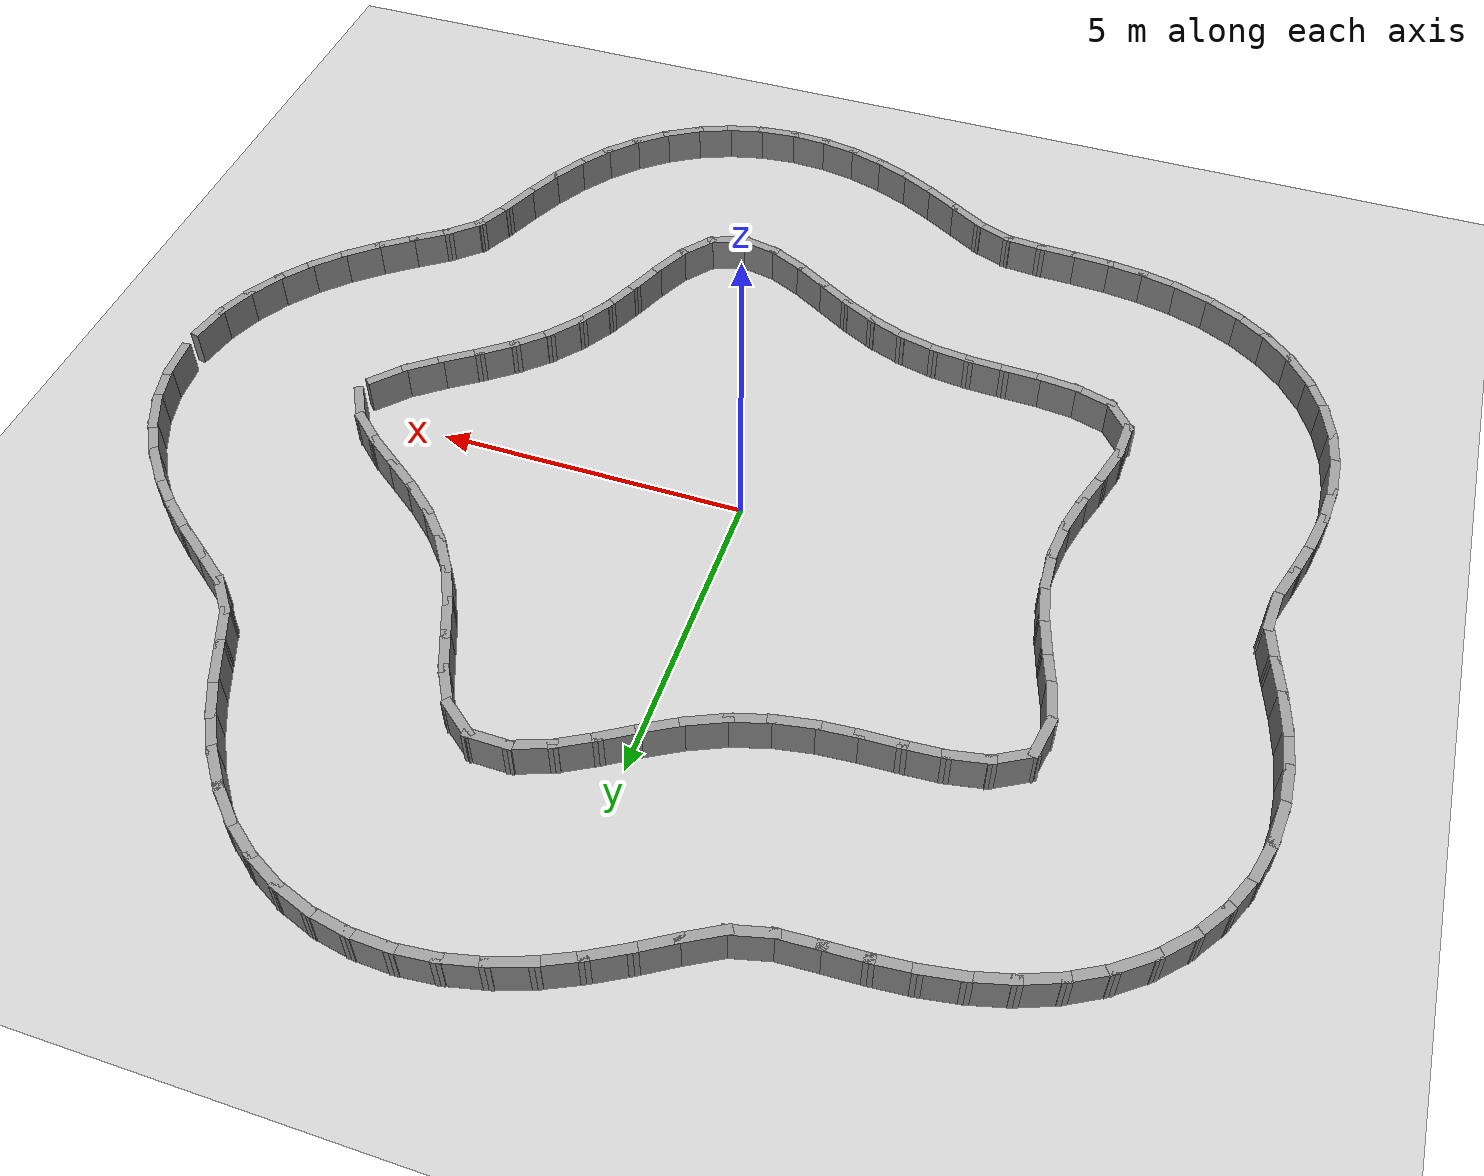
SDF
<?xml version="1.0" ?>
<sdf version='1.7'>
  <world name='default'>
    <plugin name='gazebo_ros_state' filename='libgazebo_ros_state.so'>
      <ros>
        <namespace>/</namespace>
      </ros>
      <update_rate>1000.0</update_rate>
    </plugin>

    <light name='sun' type='directional'>
      <cast_shadows>1</cast_shadows>
      <pose>0 0 10 0 -0 0</pose>
      <diffuse>0.8 0.8 0.8 1</diffuse>
      <specular>0.2 0.2 0.2 1</specular>
      <attenuation>
        <range>1000</range>
        <constant>0.9</constant>
        <linear>0.01</linear>
        <quadratic>0.001</quadratic>
      </attenuation>
      <direction>-0.5 0.1 -0.9</direction>
      <spot>
        <inner_angle>0</inner_angle>
        <outer_angle>0</outer_angle>
        <falloff>0</falloff>
      </spot>
    </light>
    <model name='ground_plane'>
      <static>1</static>
      <link name='link'>
        <collision name='collision'>
          <geometry>
            <plane>
              <normal>0 0 1</normal>
              <size>100 100</size>
            </plane>
          </geometry>
          <surface>
            <friction>
              <ode>
                <mu>100</mu>
                <mu2>50</mu2>
              </ode>
              <torsional>
                <ode/>
              </torsional>
            </friction>
            <contact>
              <ode/>
            </contact>
            <bounce/>
          </surface>
          <max_contacts>10</max_contacts>
        </collision>
        <visual name='visual'>
          <cast_shadows>0</cast_shadows>
          <geometry>
            <plane>
              <normal>0 0 1</normal>
              <size>100 100</size>
            </plane>
          </geometry>
          <material>
            <script>
              <uri>file://media/materials/scripts/gazebo.material</uri>
              <name>Gazebo/Grey</name>
            </script>
          </material>
        </visual>
        <self_collide>0</self_collide>
        <enable_wind>0</enable_wind>
        <kinematic>0</kinematic>
      </link>
    </model>
    <gravity>0 0 -9.8</gravity>
    <magnetic_field>6e-06 2.3e-05 -4.2e-05</magnetic_field>
    <atmosphere type='adiabatic'/>
    <physics type='ode'>
      <max_step_size>0.001</max_step_size>
      <real_time_factor>1</real_time_factor>
      <real_time_update_rate>1000</real_time_update_rate>
    </physics>
    <scene>
      <ambient>0.4 0.4 0.4 1</ambient>
      <background>0.7 0.7 0.7 1</background>
      <shadows>1</shadows>
    </scene>
    <audio>
      <device>default</device>
    </audio>
    <wind/>
    <spherical_coordinates>
      <surface_model>EARTH_WGS84</surface_model>
      <latitude_deg>0</latitude_deg>
      <longitude_deg>0</longitude_deg>
      <elevation>0</elevation>
      <heading_deg>0</heading_deg>
    </spherical_coordinates>
  <model name='rand_lobed_06'>
    <pose>0 0 0 0 -0 0</pose>
    <link name='Wall_0'>
      <collision name='Wall_0_Collision'>
        <geometry><box><size>0.7384 0.1500 0.6000</size></box></geometry>
        <pose>0 0 0.3000 0 -0 0</pose>
      </collision>
      <visual name='Wall_0_Visual'>
        <pose>0 0 0.3000 0 -0 0</pose>
        <geometry><box><size>0.7384 0.1500 0.6000</size></box></geometry>
        <material>
          <script>
            <uri>file://media/materials/scripts/gazebo.material</uri>
            <name>Gazebo/Grey</name>
          </script>
          <ambient>1 1 1 1</ambient>
        </material>
      </visual>
      <pose>6.3126 0.2560 0 0 -0 2.08595</pose>
    </link>
    <link name='Wall_1'>
      <collision name='Wall_1_Collision'>
        <geometry><box><size>0.7494 0.1500 0.6000</size></box></geometry>
        <pose>0 0 0.3000 0 -0 0</pose>
      </collision>
      <visual name='Wall_1_Visual'>
        <pose>0 0 0.3000 0 -0 0</pose>
        <geometry><box><size>0.7494 0.1500 0.6000</size></box></geometry>
        <material>
          <script>
            <uri>file://media/materials/scripts/gazebo.material</uri>
            <name>Gazebo/Grey</name>
          </script>
          <ambient>1 1 1 1</ambient>
        </material>
      </visual>
      <pose>5.9425 0.7098 0 0 -0 2.42072</pose>
    </link>
    <link name='Wall_2'>
      <collision name='Wall_2_Collision'>
        <geometry><box><size>0.7500 0.1500 0.6000</size></box></geometry>
        <pose>0 0 0.3000 0 -0 0</pose>
      </collision>
      <visual name='Wall_2_Visual'>
        <pose>0 0 0.3000 0 -0 0</pose>
        <geometry><box><size>0.7500 0.1500 0.6000</size></box></geometry>
        <material>
          <script>
            <uri>file://media/materials/scripts/gazebo.material</uri>
            <name>Gazebo/Grey</name>
          </script>
          <ambient>1 1 1 1</ambient>
        </material>
      </visual>
      <pose>5.4744 1.0836 0 0 -0 2.51488</pose>
    </link>
    <link name='Wall_3'>
      <collision name='Wall_3_Collision'>
        <geometry><box><size>0.7499 0.1500 0.6000</size></box></geometry>
        <pose>0 0 0.3000 0 -0 0</pose>
      </collision>
      <visual name='Wall_3_Visual'>
        <pose>0 0 0.3000 0 -0 0</pose>
        <geometry><box><size>0.7499 0.1500 0.6000</size></box></geometry>
        <material>
          <script>
            <uri>file://media/materials/scripts/gazebo.material</uri>
            <name>Gazebo/Grey</name>
          </script>
          <ambient>1 1 1 1</ambient>
        </material>
      </visual>
      <pose>4.9893 1.4365 0 0 -0 2.51041</pose>
    </link>
    <link name='Wall_4'>
      <collision name='Wall_4_Collision'>
        <geometry><box><size>0.7497 0.1500 0.6000</size></box></geometry>
        <pose>0 0 0.3000 0 -0 0</pose>
      </collision>
      <visual name='Wall_4_Visual'>
        <pose>0 0 0.3000 0 -0 0</pose>
        <geometry><box><size>0.7497 0.1500 0.6000</size></box></geometry>
        <material>
          <script>
            <uri>file://media/materials/scripts/gazebo.material</uri>
            <name>Gazebo/Grey</name>
          </script>
          <ambient>1 1 1 1</ambient>
        </material>
      </visual>
      <pose>4.5193 1.8085 0 0 -0 2.43352</pose>
    </link>
    <link name='Wall_5'>
      <collision name='Wall_5_Collision'>
        <geometry><box><size>0.7495 0.1500 0.6000</size></box></geometry>
        <pose>0 0 0.3000 0 -0 0</pose>
      </collision>
      <visual name='Wall_5_Visual'>
        <pose>0 0 0.3000 0 -0 0</pose>
        <geometry><box><size>0.7495 0.1500 0.6000</size></box></geometry>
        <material>
          <script>
            <uri>file://media/materials/scripts/gazebo.material</uri>
            <name>Gazebo/Grey</name>
          </script>
          <ambient>1 1 1 1</ambient>
        </material>
      </visual>
      <pose>4.0900 2.2254 0 0 -0 2.30842</pose>
    </link>
    <link name='Wall_6'>
      <collision name='Wall_6_Collision'>
        <geometry><box><size>0.7495 0.1500 0.6000</size></box></geometry>
        <pose>0 0 0.3000 0 -0 0</pose>
      </collision>
      <visual name='Wall_6_Visual'>
        <pose>0 0 0.3000 0 -0 0</pose>
        <geometry><box><size>0.7495 0.1500 0.6000</size></box></geometry>
        <material>
          <script>
            <uri>file://media/materials/scripts/gazebo.material</uri>
            <name>Gazebo/Grey</name>
          </script>
          <ambient>1 1 1 1</ambient>
        </material>
      </visual>
      <pose>3.7205 2.6956 0 0 -0 2.16516</pose>
    </link>
    <link name='Wall_7'>
      <collision name='Wall_7_Collision'>
        <geometry><box><size>0.7497 0.1500 0.6000</size></box></geometry>
        <pose>0 0 0.3000 0 -0 0</pose>
      </collision>
      <visual name='Wall_7_Visual'>
        <pose>0 0 0.3000 0 -0 0</pose>
        <geometry><box><size>0.7497 0.1500 0.6000</size></box></geometry>
        <material>
          <script>
            <uri>file://media/materials/scripts/gazebo.material</uri>
            <name>Gazebo/Grey</name>
          </script>
          <ambient>1 1 1 1</ambient>
        </material>
      </visual>
      <pose>3.4180 3.2118 0 0 -0 2.03660</pose>
    </link>
    <link name='Wall_8'>
      <collision name='Wall_8_Collision'>
        <geometry><box><size>0.7500 0.1500 0.6000</size></box></geometry>
        <pose>0 0 0.3000 0 -0 0</pose>
      </collision>
      <visual name='Wall_8_Visual'>
        <pose>0 0 0.3000 0 -0 0</pose>
        <geometry><box><size>0.7500 0.1500 0.6000</size></box></geometry>
        <material>
          <script>
            <uri>file://media/materials/scripts/gazebo.material</uri>
            <name>Gazebo/Grey</name>
          </script>
          <ambient>1 1 1 1</ambient>
        </material>
      </visual>
      <pose>3.1701 3.7575 0 0 -0 1.95765</pose>
    </link>
    <link name='Wall_9'>
      <collision name='Wall_9_Collision'>
        <geometry><box><size>0.7499 0.1500 0.6000</size></box></geometry>
        <pose>0 0 0.3000 0 -0 0</pose>
      </collision>
      <visual name='Wall_9_Visual'>
        <pose>0 0 0.3000 0 -0 0</pose>
        <geometry><box><size>0.7499 0.1500 0.6000</size></box></geometry>
        <material>
          <script>
            <uri>file://media/materials/scripts/gazebo.material</uri>
            <name>Gazebo/Grey</name>
          </script>
          <ambient>1 1 1 1</ambient>
        </material>
      </visual>
      <pose>2.9421 4.3124 0 0 -0 1.96361</pose>
    </link>
    <link name='Wall_10'>
      <collision name='Wall_10_Collision'>
        <geometry><box><size>0.7488 0.1500 0.6000</size></box></geometry>
        <pose>0 0 0.3000 0 -0 0</pose>
      </collision>
      <visual name='Wall_10_Visual'>
        <pose>0 0 0.3000 0 -0 0</pose>
        <geometry><box><size>0.7488 0.1500 0.6000</size></box></geometry>
        <material>
          <script>
            <uri>file://media/materials/scripts/gazebo.material</uri>
            <name>Gazebo/Grey</name>
          </script>
          <ambient>1 1 1 1</ambient>
        </material>
      </visual>
      <pose>2.6768 4.8483 0 0 -0 2.09764</pose>
    </link>
    <link name='Wall_11'>
      <collision name='Wall_11_Collision'>
        <geometry><box><size>0.7411 0.1500 0.6000</size></box></geometry>
        <pose>0 0 0.3000 0 -0 0</pose>
      </collision>
      <visual name='Wall_11_Visual'>
        <pose>0 0 0.3000 0 -0 0</pose>
        <geometry><box><size>0.7411 0.1500 0.6000</size></box></geometry>
        <material>
          <script>
            <uri>file://media/materials/scripts/gazebo.material</uri>
            <name>Gazebo/Grey</name>
          </script>
          <ambient>1 1 1 1</ambient>
        </material>
      </visual>
      <pose>2.2925 5.2879 0 0 -0 2.48318</pose>
    </link>
    <link name='Wall_12'>
      <collision name='Wall_12_Collision'>
        <geometry><box><size>0.7426 0.1500 0.6000</size></box></geometry>
        <pose>0 0 0.3000 0 -0 0</pose>
      </collision>
      <visual name='Wall_12_Visual'>
        <pose>0 0 0.3000 0 -0 0</pose>
        <geometry><box><size>0.7426 0.1500 0.6000</size></box></geometry>
        <material>
          <script>
            <uri>file://media/materials/scripts/gazebo.material</uri>
            <name>Gazebo/Grey</name>
          </script>
          <ambient>1 1 1 1</ambient>
        </material>
      </visual>
      <pose>1.7624 5.4718 0 0 -0 3.13125</pose>
    </link>
    <link name='Wall_13'>
      <collision name='Wall_13_Collision'>
        <geometry><box><size>0.7487 0.1500 0.6000</size></box></geometry>
        <pose>0 0 0.3000 0 -0 0</pose>
      </collision>
      <visual name='Wall_13_Visual'>
        <pose>0 0 0.3000 0 -0 0</pose>
        <geometry><box><size>0.7487 0.1500 0.6000</size></box></geometry>
        <material>
          <script>
            <uri>file://media/materials/scripts/gazebo.material</uri>
            <name>Gazebo/Grey</name>
          </script>
          <ambient>1 1 1 1</ambient>
        </material>
      </visual>
      <pose>1.1853 5.3713 0 0 -0 -2.78829</pose>
    </link>
    <link name='Wall_14'>
      <collision name='Wall_14_Collision'>
        <geometry><box><size>0.7498 0.1500 0.6000</size></box></geometry>
        <pose>0 0 0.3000 0 -0 0</pose>
      </collision>
      <visual name='Wall_14_Visual'>
        <pose>0 0 0.3000 0 -0 0</pose>
        <geometry><box><size>0.7498 0.1500 0.6000</size></box></geometry>
        <material>
          <script>
            <uri>file://media/materials/scripts/gazebo.material</uri>
            <name>Gazebo/Grey</name>
          </script>
          <ambient>1 1 1 1</ambient>
        </material>
      </visual>
      <pose>0.6426 5.1217 0 0 -0 -2.63271</pose>
    </link>
    <link name='Wall_15'>
      <collision name='Wall_15_Collision'>
        <geometry><box><size>0.7500 0.1500 0.6000</size></box></geometry>
        <pose>0 0 0.3000 0 -0 0</pose>
      </collision>
      <visual name='Wall_15_Visual'>
        <pose>0 0 0.3000 0 -0 0</pose>
        <geometry><box><size>0.7500 0.1500 0.6000</size></box></geometry>
        <material>
          <script>
            <uri>file://media/materials/scripts/gazebo.material</uri>
            <name>Gazebo/Grey</name>
          </script>
          <ambient>1 1 1 1</ambient>
        </material>
      </visual>
      <pose>0.1257 4.8175 0 0 -0 -2.58682</pose>
    </link>
    <link name='Wall_16'>
      <collision name='Wall_16_Collision'>
        <geometry><box><size>0.7499 0.1500 0.6000</size></box></geometry>
        <pose>0 0 0.3000 0 -0 0</pose>
      </collision>
      <visual name='Wall_16_Visual'>
        <pose>0 0 0.3000 0 -0 0</pose>
        <geometry><box><size>0.7499 0.1500 0.6000</size></box></geometry>
        <material>
          <script>
            <uri>file://media/materials/scripts/gazebo.material</uri>
            <name>Gazebo/Grey</name>
          </script>
          <ambient>1 1 1 1</ambient>
        </material>
      </visual>
      <pose>-0.3898 4.5108 0 0 -0 -2.62298</pose>
    </link>
    <link name='Wall_17'>
      <collision name='Wall_17_Collision'>
        <geometry><box><size>0.7497 0.1500 0.6000</size></box></geometry>
        <pose>0 0 0.3000 0 -0 0</pose>
      </collision>
      <visual name='Wall_17_Visual'>
        <pose>0 0 0.3000 0 -0 0</pose>
        <geometry><box><size>0.7497 0.1500 0.6000</size></box></geometry>
        <material>
          <script>
            <uri>file://media/materials/scripts/gazebo.material</uri>
            <name>Gazebo/Grey</name>
          </script>
          <ambient>1 1 1 1</ambient>
        </material>
      </visual>
      <pose>-0.9238 4.2391 0 0 -0 -2.71880</pose>
    </link>
    <link name='Wall_18'>
      <collision name='Wall_18_Collision'>
        <geometry><box><size>0.7496 0.1500 0.6000</size></box></geometry>
        <pose>0 0 0.3000 0 -0 0</pose>
      </collision>
      <visual name='Wall_18_Visual'>
        <pose>0 0 0.3000 0 -0 0</pose>
        <geometry><box><size>0.7496 0.1500 0.6000</size></box></geometry>
        <material>
          <script>
            <uri>file://media/materials/scripts/gazebo.material</uri>
            <name>Gazebo/Grey</name>
          </script>
          <ambient>1 1 1 1</ambient>
        </material>
      </visual>
      <pose>-1.4839 4.0286 0 0 -0 -2.84539</pose>
    </link>
    <link name='Wall_19'>
      <collision name='Wall_19_Collision'>
        <geometry><box><size>0.7497 0.1500 0.6000</size></box></geometry>
        <pose>0 0 0.3000 0 -0 0</pose>
      </collision>
      <visual name='Wall_19_Visual'>
        <pose>0 0 0.3000 0 -0 0</pose>
        <geometry><box><size>0.7497 0.1500 0.6000</size></box></geometry>
        <material>
          <script>
            <uri>file://media/materials/scripts/gazebo.material</uri>
            <name>Gazebo/Grey</name>
          </script>
          <ambient>1 1 1 1</ambient>
        </material>
      </visual>
      <pose>-2.0662 3.8906 0 0 -0 -2.97214</pose>
    </link>
    <link name='Wall_20'>
      <collision name='Wall_20_Collision'>
        <geometry><box><size>0.7499 0.1500 0.6000</size></box></geometry>
        <pose>0 0 0.3000 0 -0 0</pose>
      </collision>
      <visual name='Wall_20_Visual'>
        <pose>0 0 0.3000 0 -0 0</pose>
        <geometry><box><size>0.7499 0.1500 0.6000</size></box></geometry>
        <material>
          <script>
            <uri>file://media/materials/scripts/gazebo.material</uri>
            <name>Gazebo/Grey</name>
          </script>
          <ambient>1 1 1 1</ambient>
        </material>
      </visual>
      <pose>-2.6608 3.8182 0 0 -0 -3.06905</pose>
    </link>
    <link name='Wall_21'>
      <collision name='Wall_21_Collision'>
        <geometry><box><size>0.7500 0.1500 0.6000</size></box></geometry>
        <pose>0 0 0.3000 0 -0 0</pose>
      </collision>
      <visual name='Wall_21_Visual'>
        <pose>0 0 0.3000 0 -0 0</pose>
        <geometry><box><size>0.7500 0.1500 0.6000</size></box></geometry>
        <material>
          <script>
            <uri>file://media/materials/scripts/gazebo.material</uri>
            <name>Gazebo/Grey</name>
          </script>
          <ambient>1 1 1 1</ambient>
        </material>
      </visual>
      <pose>-3.2598 3.7874 0 0 -0 -3.11126</pose>
    </link>
    <link name='Wall_22'>
      <collision name='Wall_22_Collision'>
        <geometry><box><size>0.7499 0.1500 0.6000</size></box></geometry>
        <pose>0 0 0.3000 0 -0 0</pose>
      </collision>
      <visual name='Wall_22_Visual'>
        <pose>0 0 0.3000 0 -0 0</pose>
        <geometry><box><size>0.7499 0.1500 0.6000</size></box></geometry>
        <material>
          <script>
            <uri>file://media/materials/scripts/gazebo.material</uri>
            <name>Gazebo/Grey</name>
          </script>
          <ambient>1 1 1 1</ambient>
        </material>
      </visual>
      <pose>-3.8591 3.7602 0 0 -0 -3.08132</pose>
    </link>
    <link name='Wall_23'>
      <collision name='Wall_23_Collision'>
        <geometry><box><size>0.7491 0.1500 0.6000</size></box></geometry>
        <pose>0 0 0.3000 0 -0 0</pose>
      </collision>
      <visual name='Wall_23_Visual'>
        <pose>0 0 0.3000 0 -0 0</pose>
        <geometry><box><size>0.7491 0.1500 0.6000</size></box></geometry>
        <material>
          <script>
            <uri>file://media/materials/scripts/gazebo.material</uri>
            <name>Gazebo/Grey</name>
          </script>
          <ambient>1 1 1 1</ambient>
        </material>
      </visual>
      <pose>-4.4530 3.6874 0 0 -0 -2.95773</pose>
    </link>
    <link name='Wall_24'>
      <collision name='Wall_24_Collision'>
        <geometry><box><size>0.7418 0.1500 0.6000</size></box></geometry>
        <pose>0 0 0.3000 0 -0 0</pose>
      </collision>
      <visual name='Wall_24_Visual'>
        <pose>0 0 0.3000 0 -0 0</pose>
        <geometry><box><size>0.7418 0.1500 0.6000</size></box></geometry>
        <material>
          <script>
            <uri>file://media/materials/scripts/gazebo.material</uri>
            <name>Gazebo/Grey</name>
          </script>
          <ambient>1 1 1 1</ambient>
        </material>
      </visual>
      <pose>-5.0051 3.4870 0 0 -0 -2.62699</pose>
    </link>
    <link name='Wall_25'>
      <collision name='Wall_25_Collision'>
        <geometry><box><size>0.7351 0.1500 0.6000</size></box></geometry>
        <pose>0 0 0.3000 0 -0 0</pose>
      </collision>
      <visual name='Wall_25_Visual'>
        <pose>0 0 0.3000 0 -0 0</pose>
        <geometry><box><size>0.7351 0.1500 0.6000</size></box></geometry>
        <material>
          <script>
            <uri>file://media/materials/scripts/gazebo.material</uri>
            <name>Gazebo/Grey</name>
          </script>
          <ambient>1 1 1 1</ambient>
        </material>
      </visual>
      <pose>-5.3164 3.0538 0 0 -0 -1.75554</pose>
    </link>
    <link name='Wall_26'>
      <collision name='Wall_26_Collision'>
        <geometry><box><size>0.7492 0.1500 0.6000</size></box></geometry>
        <pose>0 0 0.3000 0 -0 0</pose>
      </collision>
      <visual name='Wall_26_Visual'>
        <pose>0 0 0.3000 0 -0 0</pose>
        <geometry><box><size>0.7492 0.1500 0.6000</size></box></geometry>
        <material>
          <script>
            <uri>file://media/materials/scripts/gazebo.material</uri>
            <name>Gazebo/Grey</name>
          </script>
          <ambient>1 1 1 1</ambient>
        </material>
      </visual>
      <pose>-5.3083 2.4731 0 0 -0 -1.36271</pose>
    </link>
    <link name='Wall_27'>
      <collision name='Wall_27_Collision'>
        <geometry><box><size>0.7500 0.1500 0.6000</size></box></geometry>
        <pose>0 0 0.3000 0 -0 0</pose>
      </collision>
      <visual name='Wall_27_Visual'>
        <pose>0 0 0.3000 0 -0 0</pose>
        <geometry><box><size>0.7500 0.1500 0.6000</size></box></geometry>
        <material>
          <script>
            <uri>file://media/materials/scripts/gazebo.material</uri>
            <name>Gazebo/Grey</name>
          </script>
          <ambient>1 1 1 1</ambient>
        </material>
      </visual>
      <pose>-5.1570 1.8935 0 0 -0 -1.26837</pose>
    </link>
    <link name='Wall_28'>
      <collision name='Wall_28_Collision'>
        <geometry><box><size>0.7499 0.1500 0.6000</size></box></geometry>
        <pose>0 0 0.3000 0 -0 0</pose>
      </collision>
      <visual name='Wall_28_Visual'>
        <pose>0 0 0.3000 0 -0 0</pose>
        <geometry><box><size>0.7499 0.1500 0.6000</size></box></geometry>
        <material>
          <script>
            <uri>file://media/materials/scripts/gazebo.material</uri>
            <name>Gazebo/Grey</name>
          </script>
          <ambient>1 1 1 1</ambient>
        </material>
      </visual>
      <pose>-4.9851 1.3188 0 0 -0 -1.29181</pose>
    </link>
    <link name='Wall_29'>
      <collision name='Wall_29_Collision'>
        <geometry><box><size>0.7496 0.1500 0.6000</size></box></geometry>
        <pose>0 0 0.3000 0 -0 0</pose>
      </collision>
      <visual name='Wall_29_Visual'>
        <pose>0 0 0.3000 0 -0 0</pose>
        <geometry><box><size>0.7496 0.1500 0.6000</size></box></geometry>
        <material>
          <script>
            <uri>file://media/materials/scripts/gazebo.material</uri>
            <name>Gazebo/Grey</name>
          </script>
          <ambient>1 1 1 1</ambient>
        </material>
      </visual>
      <pose>-4.8491 0.7355 0 0 -0 -1.39195</pose>
    </link>
    <link name='Wall_30'>
      <collision name='Wall_30_Collision'>
        <geometry><box><size>0.7494 0.1500 0.6000</size></box></geometry>
        <pose>0 0 0.3000 0 -0 0</pose>
      </collision>
      <visual name='Wall_30_Visual'>
        <pose>0 0 0.3000 0 -0 0</pose>
        <geometry><box><size>0.7494 0.1500 0.6000</size></box></geometry>
        <material>
          <script>
            <uri>file://media/materials/scripts/gazebo.material</uri>
            <name>Gazebo/Grey</name>
          </script>
          <ambient>1 1 1 1</ambient>
        </material>
      </visual>
      <pose>-4.7850 0.1410 0 0 -0 -1.53478</pose>
    </link>
    <link name='Wall_31'>
      <collision name='Wall_31_Collision'>
        <geometry><box><size>0.7495 0.1500 0.6000</size></box></geometry>
        <pose>0 0 0.3000 0 -0 0</pose>
      </collision>
      <visual name='Wall_31_Visual'>
        <pose>0 0 0.3000 0 -0 0</pose>
        <geometry><box><size>0.7495 0.1500 0.6000</size></box></geometry>
        <material>
          <script>
            <uri>file://media/materials/scripts/gazebo.material</uri>
            <name>Gazebo/Grey</name>
          </script>
          <ambient>1 1 1 1</ambient>
        </material>
      </visual>
      <pose>-4.8085 -0.4563 0 0 -0 -1.68550</pose>
    </link>
    <link name='Wall_32'>
      <collision name='Wall_32_Collision'>
        <geometry><box><size>0.7497 0.1500 0.6000</size></box></geometry>
        <pose>0 0 0.3000 0 -0 0</pose>
      </collision>
      <visual name='Wall_32_Visual'>
        <pose>0 0 0.3000 0 -0 0</pose>
        <geometry><box><size>0.7497 0.1500 0.6000</size></box></geometry>
        <material>
          <script>
            <uri>file://media/materials/scripts/gazebo.material</uri>
            <name>Gazebo/Grey</name>
          </script>
          <ambient>1 1 1 1</ambient>
        </material>
      </visual>
      <pose>-4.9139 -1.0454 0 0 -0 -1.81005</pose>
    </link>
    <link name='Wall_33'>
      <collision name='Wall_33_Collision'>
        <geometry><box><size>0.7500 0.1500 0.6000</size></box></geometry>
        <pose>0 0 0.3000 0 -0 0</pose>
      </collision>
      <visual name='Wall_33_Visual'>
        <pose>0 0 0.3000 0 -0 0</pose>
        <geometry><box><size>0.7500 0.1500 0.6000</size></box></geometry>
        <material>
          <script>
            <uri>file://media/materials/scripts/gazebo.material</uri>
            <name>Gazebo/Grey</name>
          </script>
          <ambient>1 1 1 1</ambient>
        </material>
      </visual>
      <pose>-5.0745 -1.6231 0 0 -0 -1.87388</pose>
    </link>
    <link name='Wall_34'>
      <collision name='Wall_34_Collision'>
        <geometry><box><size>0.7498 0.1500 0.6000</size></box></geometry>
        <pose>0 0 0.3000 0 -0 0</pose>
      </collision>
      <visual name='Wall_34_Visual'>
        <pose>0 0 0.3000 0 -0 0</pose>
        <geometry><box><size>0.7498 0.1500 0.6000</size></box></geometry>
        <material>
          <script>
            <uri>file://media/materials/scripts/gazebo.material</uri>
            <name>Gazebo/Grey</name>
          </script>
          <ambient>1 1 1 1</ambient>
        </material>
      </visual>
      <pose>-5.2444 -2.1983 0 0 -0 -1.84209</pose>
    </link>
    <link name='Wall_35'>
      <collision name='Wall_35_Collision'>
        <geometry><box><size>0.7469 0.1500 0.6000</size></box></geometry>
        <pose>0 0 0.3000 0 -0 0</pose>
      </collision>
      <visual name='Wall_35_Visual'>
        <pose>0 0 0.3000 0 -0 0</pose>
        <geometry><box><size>0.7469 0.1500 0.6000</size></box></geometry>
        <material>
          <script>
            <uri>file://media/materials/scripts/gazebo.material</uri>
            <name>Gazebo/Grey</name>
          </script>
          <ambient>1 1 1 1</ambient>
        </material>
      </visual>
      <pose>-5.3463 -2.7849 0 0 -0 -1.64294</pose>
    </link>
    <link name='Wall_36'>
      <collision name='Wall_36_Collision'>
        <geometry><box><size>0.7226 0.1500 0.6000</size></box></geometry>
        <pose>0 0 0.3000 0 -0 0</pose>
      </collision>
      <visual name='Wall_36_Visual'>
        <pose>0 0 0.3000 0 -0 0</pose>
        <geometry><box><size>0.7226 0.1500 0.6000</size></box></geometry>
        <material>
          <script>
            <uri>file://media/materials/scripts/gazebo.material</uri>
            <name>Gazebo/Grey</name>
          </script>
          <ambient>1 1 1 1</ambient>
        </material>
      </visual>
      <pose>-5.1893 -3.3064 0 0 -0 -0.89751</pose>
    </link>
    <link name='Wall_37'>
      <collision name='Wall_37_Collision'>
        <geometry><box><size>0.7479 0.1500 0.6000</size></box></geometry>
        <pose>0 0 0.3000 0 -0 0</pose>
      </collision>
      <visual name='Wall_37_Visual'>
        <pose>0 0 0.3000 0 -0 0</pose>
        <geometry><box><size>0.7479 0.1500 0.6000</size></box></geometry>
        <material>
          <script>
            <uri>file://media/materials/scripts/gazebo.material</uri>
            <name>Gazebo/Grey</name>
          </script>
          <ambient>1 1 1 1</ambient>
        </material>
      </visual>
      <pose>-4.7247 -3.6171 0 0 -0 -0.29486</pose>
    </link>
    <link name='Wall_38'>
      <collision name='Wall_38_Collision'>
        <geometry><box><size>0.7497 0.1500 0.6000</size></box></geometry>
        <pose>0 0 0.3000 0 -0 0</pose>
      </collision>
      <visual name='Wall_38_Visual'>
        <pose>0 0 0.3000 0 -0 0</pose>
        <geometry><box><size>0.7497 0.1500 0.6000</size></box></geometry>
        <material>
          <script>
            <uri>file://media/materials/scripts/gazebo.material</uri>
            <name>Gazebo/Grey</name>
          </script>
          <ambient>1 1 1 1</ambient>
        </material>
      </visual>
      <pose>-4.1404 -3.7353 0 0 -0 -0.10435</pose>
    </link>
    <link name='Wall_39'>
      <collision name='Wall_39_Collision'>
        <geometry><box><size>0.7500 0.1500 0.6000</size></box></geometry>
        <pose>0 0 0.3000 0 -0 0</pose>
      </collision>
      <visual name='Wall_39_Visual'>
        <pose>0 0 0.3000 0 -0 0</pose>
        <geometry><box><size>0.7500 0.1500 0.6000</size></box></geometry>
        <material>
          <script>
            <uri>file://media/materials/scripts/gazebo.material</uri>
            <name>Gazebo/Grey</name>
          </script>
          <ambient>1 1 1 1</ambient>
        </material>
      </visual>
      <pose>-3.5424 -3.7769 0 0 -0 -0.03458</pose>
    </link>
    <link name='Wall_40'>
      <collision name='Wall_40_Collision'>
        <geometry><box><size>0.7499 0.1500 0.6000</size></box></geometry>
        <pose>0 0 0.3000 0 -0 0</pose>
      </collision>
      <visual name='Wall_40_Visual'>
        <pose>0 0 0.3000 0 -0 0</pose>
        <geometry><box><size>0.7499 0.1500 0.6000</size></box></geometry>
        <material>
          <script>
            <uri>file://media/materials/scripts/gazebo.material</uri>
            <name>Gazebo/Grey</name>
          </script>
          <ambient>1 1 1 1</ambient>
        </material>
      </visual>
      <pose>-2.9429 -3.8006 0 0 -0 -0.04460</pose>
    </link>
    <link name='Wall_41'>
      <collision name='Wall_41_Collision'>
        <geometry><box><size>0.7497 0.1500 0.6000</size></box></geometry>
        <pose>0 0 0.3000 0 -0 0</pose>
      </collision>
      <visual name='Wall_41_Visual'>
        <pose>0 0 0.3000 0 -0 0</pose>
        <geometry><box><size>0.7497 0.1500 0.6000</size></box></geometry>
        <material>
          <script>
            <uri>file://media/materials/scripts/gazebo.material</uri>
            <name>Gazebo/Grey</name>
          </script>
          <ambient>1 1 1 1</ambient>
        </material>
      </visual>
      <pose>-2.3455 -3.8494 0 0 -0 -0.11838</pose>
    </link>
    <link name='Wall_42'>
      <collision name='Wall_42_Collision'>
        <geometry><box><size>0.7496 0.1500 0.6000</size></box></geometry>
        <pose>0 0 0.3000 0 -0 0</pose>
      </collision>
      <visual name='Wall_42_Visual'>
        <pose>0 0 0.3000 0 -0 0</pose>
        <geometry><box><size>0.7496 0.1500 0.6000</size></box></geometry>
        <material>
          <script>
            <uri>file://media/materials/scripts/gazebo.material</uri>
            <name>Gazebo/Grey</name>
          </script>
          <ambient>1 1 1 1</ambient>
        </material>
      </visual>
      <pose>-1.7561 -3.9545 0 0 -0 -0.23457</pose>
    </link>
    <link name='Wall_43'>
      <collision name='Wall_43_Collision'>
        <geometry><box><size>0.7496 0.1500 0.6000</size></box></geometry>
        <pose>0 0 0.3000 0 -0 0</pose>
      </collision>
      <visual name='Wall_43_Visual'>
        <pose>0 0 0.3000 0 -0 0</pose>
        <geometry><box><size>0.7496 0.1500 0.6000</size></box></geometry>
        <material>
          <script>
            <uri>file://media/materials/scripts/gazebo.material</uri>
            <name>Gazebo/Grey</name>
          </script>
          <ambient>1 1 1 1</ambient>
        </material>
      </visual>
      <pose>-1.1845 -4.1312 0 0 -0 -0.36510</pose>
    </link>
    <link name='Wall_44'>
      <collision name='Wall_44_Collision'>
        <geometry><box><size>0.7498 0.1500 0.6000</size></box></geometry>
        <pose>0 0 0.3000 0 -0 0</pose>
      </collision>
      <visual name='Wall_44_Visual'>
        <pose>0 0 0.3000 0 -0 0</pose>
        <geometry><box><size>0.7498 0.1500 0.6000</size></box></geometry>
        <material>
          <script>
            <uri>file://media/materials/scripts/gazebo.material</uri>
            <name>Gazebo/Grey</name>
          </script>
          <ambient>1 1 1 1</ambient>
        </material>
      </visual>
      <pose>-0.6384 -4.3765 0 0 -0 -0.47925</pose>
    </link>
    <link name='Wall_45'>
      <collision name='Wall_45_Collision'>
        <geometry><box><size>0.7500 0.1500 0.6000</size></box></geometry>
        <pose>0 0 0.3000 0 -0 0</pose>
      </collision>
      <visual name='Wall_45_Visual'>
        <pose>0 0 0.3000 0 -0 0</pose>
        <geometry><box><size>0.7500 0.1500 0.6000</size></box></geometry>
        <material>
          <script>
            <uri>file://media/materials/scripts/gazebo.material</uri>
            <name>Gazebo/Grey</name>
          </script>
          <ambient>1 1 1 1</ambient>
        </material>
      </visual>
      <pose>-0.1160 -4.6708 0 0 -0 -0.54672</pose>
    </link>
    <link name='Wall_46'>
      <collision name='Wall_46_Collision'>
        <geometry><box><size>0.7499 0.1500 0.6000</size></box></geometry>
        <pose>0 0 0.3000 0 -0 0</pose>
      </collision>
      <visual name='Wall_46_Visual'>
        <pose>0 0 0.3000 0 -0 0</pose>
        <geometry><box><size>0.7499 0.1500 0.6000</size></box></geometry>
        <material>
          <script>
            <uri>file://media/materials/scripts/gazebo.material</uri>
            <name>Gazebo/Grey</name>
          </script>
          <ambient>1 1 1 1</ambient>
        </material>
      </visual>
      <pose>0.3972 -4.9815 0 0 -0 -0.54201</pose>
    </link>
    <link name='Wall_47'>
      <collision name='Wall_47_Collision'>
        <geometry><box><size>0.7494 0.1500 0.6000</size></box></geometry>
        <pose>0 0 0.3000 0 -0 0</pose>
      </collision>
      <visual name='Wall_47_Visual'>
        <pose>0 0 0.3000 0 -0 0</pose>
        <geometry><box><size>0.7494 0.1500 0.6000</size></box></geometry>
        <material>
          <script>
            <uri>file://media/materials/scripts/gazebo.material</uri>
            <name>Gazebo/Grey</name>
          </script>
          <ambient>1 1 1 1</ambient>
        </material>
      </visual>
      <pose>0.9249 -5.2648 0 0 -0 -0.44341</pose>
    </link>
    <link name='Wall_48'>
      <collision name='Wall_48_Collision'>
        <geometry><box><size>0.7468 0.1500 0.6000</size></box></geometry>
        <pose>0 0 0.3000 0 -0 0</pose>
      </collision>
      <visual name='Wall_48_Visual'>
        <pose>0 0 0.3000 0 -0 0</pose>
        <geometry><box><size>0.7468 0.1500 0.6000</size></box></geometry>
        <material>
          <script>
            <uri>file://media/materials/scripts/gazebo.material</uri>
            <name>Gazebo/Grey</name>
          </script>
          <ambient>1 1 1 1</ambient>
        </material>
      </visual>
      <pose>1.4881 -5.4528 0 0 -0 -0.20037</pose>
    </link>
    <link name='Wall_49'>
      <collision name='Wall_49_Collision'>
        <geometry><box><size>0.7370 0.1500 0.6000</size></box></geometry>
        <pose>0 0 0.3000 0 -0 0</pose>
      </collision>
      <visual name='Wall_49_Visual'>
        <pose>0 0 0.3000 0 -0 0</pose>
        <geometry><box><size>0.7370 0.1500 0.6000</size></box></geometry>
        <material>
          <script>
            <uri>file://media/materials/scripts/gazebo.material</uri>
            <name>Gazebo/Grey</name>
          </script>
          <ambient>1 1 1 1</ambient>
        </material>
      </visual>
      <pose>2.0565 -5.4122 0 0 -0 0.34736</pose>
    </link>
    <link name='Wall_50'>
      <collision name='Wall_50_Collision'>
        <geometry><box><size>0.7468 0.1500 0.6000</size></box></geometry>
        <pose>0 0 0.3000 0 -0 0</pose>
      </collision>
      <visual name='Wall_50_Visual'>
        <pose>0 0 0.3000 0 -0 0</pose>
        <geometry><box><size>0.7468 0.1500 0.6000</size></box></geometry>
        <material>
          <script>
            <uri>file://media/materials/scripts/gazebo.material</uri>
            <name>Gazebo/Grey</name>
          </script>
          <ambient>1 1 1 1</ambient>
        </material>
      </visual>
      <pose>2.5160 -5.0770 0 0 -0 0.90844</pose>
    </link>
    <link name='Wall_51'>
      <collision name='Wall_51_Collision'>
        <geometry><box><size>0.7496 0.1500 0.6000</size></box></geometry>
        <pose>0 0 0.3000 0 -0 0</pose>
      </collision>
      <visual name='Wall_51_Visual'>
        <pose>0 0 0.3000 0 -0 0</pose>
        <geometry><box><size>0.7496 0.1500 0.6000</size></box></geometry>
        <material>
          <script>
            <uri>file://media/materials/scripts/gazebo.material</uri>
            <name>Gazebo/Grey</name>
          </script>
          <ambient>1 1 1 1</ambient>
        </material>
      </visual>
      <pose>2.8261 -4.5700 0 0 -0 1.13472</pose>
    </link>
    <link name='Wall_52'>
      <collision name='Wall_52_Collision'>
        <geometry><box><size>0.7500 0.1500 0.6000</size></box></geometry>
        <pose>0 0 0.3000 0 -0 0</pose>
      </collision>
      <visual name='Wall_52_Visual'>
        <pose>0 0 0.3000 0 -0 0</pose>
        <geometry><box><size>0.7500 0.1500 0.6000</size></box></geometry>
        <material>
          <script>
            <uri>file://media/materials/scripts/gazebo.material</uri>
            <name>Gazebo/Grey</name>
          </script>
          <ambient>1 1 1 1</ambient>
        </material>
      </visual>
      <pose>3.0632 -4.0193 0 0 -0 1.19387</pose>
    </link>
    <link name='Wall_53'>
      <collision name='Wall_53_Collision'>
        <geometry><box><size>0.7498 0.1500 0.6000</size></box></geometry>
        <pose>0 0 0.3000 0 -0 0</pose>
      </collision>
      <visual name='Wall_53_Visual'>
        <pose>0 0 0.3000 0 -0 0</pose>
        <geometry><box><size>0.7498 0.1500 0.6000</size></box></geometry>
        <material>
          <script>
            <uri>file://media/materials/scripts/gazebo.material</uri>
            <name>Gazebo/Grey</name>
          </script>
          <ambient>1 1 1 1</ambient>
        </material>
      </visual>
      <pose>3.2959 -3.4665 0 0 -0 1.15057</pose>
    </link>
    <link name='Wall_54'>
      <collision name='Wall_54_Collision'>
        <geometry><box><size>0.7496 0.1500 0.6000</size></box></geometry>
        <pose>0 0 0.3000 0 -0 0</pose>
      </collision>
      <visual name='Wall_54_Visual'>
        <pose>0 0 0.3000 0 -0 0</pose>
        <geometry><box><size>0.7496 0.1500 0.6000</size></box></geometry>
        <material>
          <script>
            <uri>file://media/materials/scripts/gazebo.material</uri>
            <name>Gazebo/Grey</name>
          </script>
          <ambient>1 1 1 1</ambient>
        </material>
      </visual>
      <pose>3.5698 -2.9340 0 0 -0 1.04101</pose>
    </link>
    <link name='Wall_55'>
      <collision name='Wall_55_Collision'>
        <geometry><box><size>0.7495 0.1500 0.6000</size></box></geometry>
        <pose>0 0 0.3000 0 -0 0</pose>
      </collision>
      <visual name='Wall_55_Visual'>
        <pose>0 0 0.3000 0 -0 0</pose>
        <geometry><box><size>0.7495 0.1500 0.6000</size></box></geometry>
        <material>
          <script>
            <uri>file://media/materials/scripts/gazebo.material</uri>
            <name>Gazebo/Grey</name>
          </script>
          <ambient>1 1 1 1</ambient>
        </material>
      </visual>
      <pose>3.9075 -2.4405 0 0 -0 0.90035</pose>
    </link>
    <link name='Wall_56'>
      <collision name='Wall_56_Collision'>
        <geometry><box><size>0.7496 0.1500 0.6000</size></box></geometry>
        <pose>0 0 0.3000 0 -0 0</pose>
      </collision>
      <visual name='Wall_56_Visual'>
        <pose>0 0 0.3000 0 -0 0</pose>
        <geometry><box><size>0.7496 0.1500 0.6000</size></box></geometry>
        <material>
          <script>
            <uri>file://media/materials/scripts/gazebo.material</uri>
            <name>Gazebo/Grey</name>
          </script>
          <ambient>1 1 1 1</ambient>
        </material>
      </visual>
      <pose>4.3105 -1.9985 0 0 -0 0.76277</pose>
    </link>
    <link name='Wall_57'>
      <collision name='Wall_57_Collision'>
        <geometry><box><size>0.7499 0.1500 0.6000</size></box></geometry>
        <pose>0 0 0.3000 0 -0 0</pose>
      </collision>
      <visual name='Wall_57_Visual'>
        <pose>0 0 0.3000 0 -0 0</pose>
        <geometry><box><size>0.7499 0.1500 0.6000</size></box></geometry>
        <material>
          <script>
            <uri>file://media/materials/scripts/gazebo.material</uri>
            <name>Gazebo/Grey</name>
          </script>
          <ambient>1 1 1 1</ambient>
        </material>
      </visual>
      <pose>4.7642 -1.6075 0 0 -0 0.65969</pose>
    </link>
    <link name='Wall_58'>
      <collision name='Wall_58_Collision'>
        <geometry><box><size>0.7500 0.1500 0.6000</size></box></geometry>
        <pose>0 0 0.3000 0 -0 0</pose>
      </collision>
      <visual name='Wall_58_Visual'>
        <pose>0 0 0.3000 0 -0 0</pose>
        <geometry><box><size>0.7500 0.1500 0.6000</size></box></geometry>
        <material>
          <script>
            <uri>file://media/materials/scripts/gazebo.material</uri>
            <name>Gazebo/Grey</name>
          </script>
          <ambient>1 1 1 1</ambient>
        </material>
      </visual>
      <pose>5.2457 -1.2498 0 0 -0 0.61848</pose>
    </link>
    <link name='Wall_59'>
      <collision name='Wall_59_Collision'>
        <geometry><box><size>0.7498 0.1500 0.6000</size></box></geometry>
        <pose>0 0 0.3000 0 -0 0</pose>
      </collision>
      <visual name='Wall_59_Visual'>
        <pose>0 0 0.3000 0 -0 0</pose>
        <geometry><box><size>0.7498 0.1500 0.6000</size></box></geometry>
        <material>
          <script>
            <uri>file://media/materials/scripts/gazebo.material</uri>
            <name>Gazebo/Grey</name>
          </script>
          <ambient>1 1 1 1</ambient>
        </material>
      </visual>
      <pose>5.7267 -0.8916 0 0 -0 0.66139</pose>
    </link>
    <link name='Wall_60'>
      <collision name='Wall_60_Collision'>
        <geometry><box><size>0.7479 0.1500 0.6000</size></box></geometry>
        <pose>0 0 0.3000 0 -0 0</pose>
      </collision>
      <visual name='Wall_60_Visual'>
        <pose>0 0 0.3000 0 -0 0</pose>
        <geometry><box><size>0.7479 0.1500 0.6000</size></box></geometry>
        <material>
          <script>
            <uri>file://media/materials/scripts/gazebo.material</uri>
            <name>Gazebo/Grey</name>
          </script>
          <ambient>1 1 1 1</ambient>
        </material>
      </visual>
      <pose>6.1634 -0.4853 0 0 -0 0.83794</pose>
    </link>
    <link name='Wall_61'>
      <collision name='Wall_61_Collision'>
        <geometry><box><size>0.7492 0.1500 0.6000</size></box></geometry>
        <pose>0 0 0.3000 0 -0 0</pose>
      </collision>
      <visual name='Wall_61_Visual'>
        <pose>0 0 0.3000 0 -0 0</pose>
        <geometry><box><size>0.7492 0.1500 0.6000</size></box></geometry>
        <material>
          <script>
            <uri>file://media/materials/scripts/gazebo.material</uri>
            <name>Gazebo/Grey</name>
          </script>
          <ambient>1 1 1 1</ambient>
        </material>
      </visual>
      <pose>9.5967 0.2985 0 0 -0 1.65788</pose>
    </link>
    <link name='Wall_62'>
      <collision name='Wall_62_Collision'>
        <geometry><box><size>0.7493 0.1500 0.6000</size></box></geometry>
        <pose>0 0 0.3000 0 -0 0</pose>
      </collision>
      <visual name='Wall_62_Visual'>
        <pose>0 0 0.3000 0 -0 0</pose>
        <geometry><box><size>0.7493 0.1500 0.6000</size></box></geometry>
        <material>
          <script>
            <uri>file://media/materials/scripts/gazebo.material</uri>
            <name>Gazebo/Grey</name>
          </script>
          <ambient>1 1 1 1</ambient>
        </material>
      </visual>
      <pose>9.4942 0.8867 0 0 -0 1.82860</pose>
    </link>
    <link name='Wall_63'>
      <collision name='Wall_63_Collision'>
        <geometry><box><size>0.7494 0.1500 0.6000</size></box></geometry>
        <pose>0 0 0.3000 0 -0 0</pose>
      </collision>
      <visual name='Wall_63_Visual'>
        <pose>0 0 0.3000 0 -0 0</pose>
        <geometry><box><size>0.7494 0.1500 0.6000</size></box></geometry>
        <material>
          <script>
            <uri>file://media/materials/scripts/gazebo.material</uri>
            <name>Gazebo/Grey</name>
          </script>
          <ambient>1 1 1 1</ambient>
        </material>
      </visual>
      <pose>9.2957 1.4501 0 0 -0 1.99055</pose>
    </link>
    <link name='Wall_64'>
      <collision name='Wall_64_Collision'>
        <geometry><box><size>0.7495 0.1500 0.6000</size></box></geometry>
        <pose>0 0 0.3000 0 -0 0</pose>
      </collision>
      <visual name='Wall_64_Visual'>
        <pose>0 0 0.3000 0 -0 0</pose>
        <geometry><box><size>0.7495 0.1500 0.6000</size></box></geometry>
        <material>
          <script>
            <uri>file://media/materials/scripts/gazebo.material</uri>
            <name>Gazebo/Grey</name>
          </script>
          <ambient>1 1 1 1</ambient>
        </material>
      </visual>
      <pose>9.0124 1.9766 0 0 -0 2.13853</pose>
    </link>
    <link name='Wall_65'>
      <collision name='Wall_65_Collision'>
        <geometry><box><size>0.7496 0.1500 0.6000</size></box></geometry>
        <pose>0 0 0.3000 0 -0 0</pose>
      </collision>
      <visual name='Wall_65_Visual'>
        <pose>0 0 0.3000 0 -0 0</pose>
        <geometry><box><size>0.7496 0.1500 0.6000</size></box></geometry>
        <material>
          <script>
            <uri>file://media/materials/scripts/gazebo.material</uri>
            <name>Gazebo/Grey</name>
          </script>
          <ambient>1 1 1 1</ambient>
        </material>
      </visual>
      <pose>8.6584 2.4589 0 0 -0 2.26909</pose>
    </link>
    <link name='Wall_66'>
      <collision name='Wall_66_Collision'>
        <geometry><box><size>0.7498 0.1500 0.6000</size></box></geometry>
        <pose>0 0 0.3000 0 -0 0</pose>
      </collision>
      <visual name='Wall_66_Visual'>
        <pose>0 0 0.3000 0 -0 0</pose>
        <geometry><box><size>0.7498 0.1500 0.6000</size></box></geometry>
        <material>
          <script>
            <uri>file://media/materials/scripts/gazebo.material</uri>
            <name>Gazebo/Grey</name>
          </script>
          <ambient>1 1 1 1</ambient>
        </material>
      </visual>
      <pose>8.2489 2.8958 0 0 -0 2.37871</pose>
    </link>
    <link name='Wall_67'>
      <collision name='Wall_67_Collision'>
        <geometry><box><size>0.7499 0.1500 0.6000</size></box></geometry>
        <pose>0 0 0.3000 0 -0 0</pose>
      </collision>
      <visual name='Wall_67_Visual'>
        <pose>0 0 0.3000 0 -0 0</pose>
        <geometry><box><size>0.7499 0.1500 0.6000</size></box></geometry>
        <material>
          <script>
            <uri>file://media/materials/scripts/gazebo.material</uri>
            <name>Gazebo/Grey</name>
          </script>
          <ambient>1 1 1 1</ambient>
        </material>
      </visual>
      <pose>7.7984 3.2910 0 0 -0 2.46405</pose>
    </link>
    <link name='Wall_68'>
      <collision name='Wall_68_Collision'>
        <geometry><box><size>0.7500 0.1500 0.6000</size></box></geometry>
        <pose>0 0 0.3000 0 -0 0</pose>
      </collision>
      <visual name='Wall_68_Visual'>
        <pose>0 0 0.3000 0 -0 0</pose>
        <geometry><box><size>0.7500 0.1500 0.6000</size></box></geometry>
        <material>
          <script>
            <uri>file://media/materials/scripts/gazebo.material</uri>
            <name>Gazebo/Grey</name>
          </script>
          <ambient>1 1 1 1</ambient>
        </material>
      </visual>
      <pose>7.3215 3.6546 0 0 -0 2.51645</pose>
    </link>
    <link name='Wall_69'>
      <collision name='Wall_69_Collision'>
        <geometry><box><size>0.7499 0.1500 0.6000</size></box></geometry>
        <pose>0 0 0.3000 0 -0 0</pose>
      </collision>
      <visual name='Wall_69_Visual'>
        <pose>0 0 0.3000 0 -0 0</pose>
        <geometry><box><size>0.7499 0.1500 0.6000</size></box></geometry>
        <material>
          <script>
            <uri>file://media/materials/scripts/gazebo.material</uri>
            <name>Gazebo/Grey</name>
          </script>
          <ambient>1 1 1 1</ambient>
        </material>
      </visual>
      <pose>6.8372 4.0087 0 0 -0 2.50422</pose>
    </link>
    <link name='Wall_70'>
      <collision name='Wall_70_Collision'>
        <geometry><box><size>0.7440 0.1500 0.6000</size></box></geometry>
        <pose>0 0 0.3000 0 -0 0</pose>
      </collision>
      <visual name='Wall_70_Visual'>
        <pose>0 0 0.3000 0 -0 0</pose>
        <geometry><box><size>0.7440 0.1500 0.6000</size></box></geometry>
        <material>
          <script>
            <uri>file://media/materials/scripts/gazebo.material</uri>
            <name>Gazebo/Grey</name>
          </script>
          <ambient>1 1 1 1</ambient>
        </material>
      </visual>
      <pose>6.4117 4.4199 0 0 -0 2.24082</pose>
    </link>
    <link name='Wall_71'>
      <collision name='Wall_71_Collision'>
        <geometry><box><size>0.7499 0.1500 0.6000</size></box></geometry>
        <pose>0 0 0.3000 0 -0 0</pose>
      </collision>
      <visual name='Wall_71_Visual'>
        <pose>0 0 0.3000 0 -0 0</pose>
        <geometry><box><size>0.7499 0.1500 0.6000</size></box></geometry>
        <material>
          <script>
            <uri>file://media/materials/scripts/gazebo.material</uri>
            <name>Gazebo/Grey</name>
          </script>
          <ambient>1 1 1 1</ambient>
        </material>
      </visual>
      <pose>6.1123 4.9298 0 0 -0 1.96399</pose>
    </link>
    <link name='Wall_72'>
      <collision name='Wall_72_Collision'>
        <geometry><box><size>0.7500 0.1500 0.6000</size></box></geometry>
        <pose>0 0 0.3000 0 -0 0</pose>
      </collision>
      <visual name='Wall_72_Visual'>
        <pose>0 0 0.3000 0 -0 0</pose>
        <geometry><box><size>0.7500 0.1500 0.6000</size></box></geometry>
        <material>
          <script>
            <uri>file://media/materials/scripts/gazebo.material</uri>
            <name>Gazebo/Grey</name>
          </script>
          <ambient>1 1 1 1</ambient>
        </material>
      </visual>
      <pose>5.8839 5.4845 0 0 -0 1.95895</pose>
    </link>
    <link name='Wall_73'>
      <collision name='Wall_73_Collision'>
        <geometry><box><size>0.7498 0.1500 0.6000</size></box></geometry>
        <pose>0 0 0.3000 0 -0 0</pose>
      </collision>
      <visual name='Wall_73_Visual'>
        <pose>0 0 0.3000 0 -0 0</pose>
        <geometry><box><size>0.7498 0.1500 0.6000</size></box></geometry>
        <material>
          <script>
            <uri>file://media/materials/scripts/gazebo.material</uri>
            <name>Gazebo/Grey</name>
          </script>
          <ambient>1 1 1 1</ambient>
        </material>
      </visual>
      <pose>5.6395 6.0320 0 0 -0 2.02232</pose>
    </link>
    <link name='Wall_74'>
      <collision name='Wall_74_Collision'>
        <geometry><box><size>0.7497 0.1500 0.6000</size></box></geometry>
        <pose>0 0 0.3000 0 -0 0</pose>
      </collision>
      <visual name='Wall_74_Visual'>
        <pose>0 0 0.3000 0 -0 0</pose>
        <geometry><box><size>0.7497 0.1500 0.6000</size></box></geometry>
        <material>
          <script>
            <uri>file://media/materials/scripts/gazebo.material</uri>
            <name>Gazebo/Grey</name>
          </script>
          <ambient>1 1 1 1</ambient>
        </material>
      </visual>
      <pose>5.3528 6.5581 0 0 -0 2.11734</pose>
    </link>
    <link name='Wall_75'>
      <collision name='Wall_75_Collision'>
        <geometry><box><size>0.7496 0.1500 0.6000</size></box></geometry>
        <pose>0 0 0.3000 0 -0 0</pose>
      </collision>
      <visual name='Wall_75_Visual'>
        <pose>0 0 0.3000 0 -0 0</pose>
        <geometry><box><size>0.7496 0.1500 0.6000</size></box></geometry>
        <material>
          <script>
            <uri>file://media/materials/scripts/gazebo.material</uri>
            <name>Gazebo/Grey</name>
          </script>
          <ambient>1 1 1 1</ambient>
        </material>
      </visual>
      <pose>5.0126 7.0507 0 0 -0 2.23292</pose>
    </link>
    <link name='Wall_76'>
      <collision name='Wall_76_Collision'>
        <geometry><box><size>0.7495 0.1500 0.6000</size></box></geometry>
        <pose>0 0 0.3000 0 -0 0</pose>
      </collision>
      <visual name='Wall_76_Visual'>
        <pose>0 0 0.3000 0 -0 0</pose>
        <geometry><box><size>0.7495 0.1500 0.6000</size></box></geometry>
        <material>
          <script>
            <uri>file://media/materials/scripts/gazebo.material</uri>
            <name>Gazebo/Grey</name>
          </script>
          <ambient>1 1 1 1</ambient>
        </material>
      </visual>
      <pose>4.6148 7.4975 0 0 -0 2.36365</pose>
    </link>
    <link name='Wall_77'>
      <collision name='Wall_77_Collision'>
        <geometry><box><size>0.7495 0.1500 0.6000</size></box></geometry>
        <pose>0 0 0.3000 0 -0 0</pose>
      </collision>
      <visual name='Wall_77_Visual'>
        <pose>0 0 0.3000 0 -0 0</pose>
        <geometry><box><size>0.7495 0.1500 0.6000</size></box></geometry>
        <material>
          <script>
            <uri>file://media/materials/scripts/gazebo.material</uri>
            <name>Gazebo/Grey</name>
          </script>
          <ambient>1 1 1 1</ambient>
        </material>
      </visual>
      <pose>4.1601 7.8860 0 0 -0 2.50535</pose>
    </link>
    <link name='Wall_78'>
      <collision name='Wall_78_Collision'>
        <geometry><box><size>0.7494 0.1500 0.6000</size></box></geometry>
        <pose>0 0 0.3000 0 -0 0</pose>
      </collision>
      <visual name='Wall_78_Visual'>
        <pose>0 0 0.3000 0 -0 0</pose>
        <geometry><box><size>0.7494 0.1500 0.6000</size></box></geometry>
        <material>
          <script>
            <uri>file://media/materials/scripts/gazebo.material</uri>
            <name>Gazebo/Grey</name>
          </script>
          <ambient>1 1 1 1</ambient>
        </material>
      </visual>
      <pose>3.6542 8.2044 0 0 -0 2.65415</pose>
    </link>
    <link name='Wall_79'>
      <collision name='Wall_79_Collision'>
        <geometry><box><size>0.7494 0.1500 0.6000</size></box></geometry>
        <pose>0 0 0.3000 0 -0 0</pose>
      </collision>
      <visual name='Wall_79_Visual'>
        <pose>0 0 0.3000 0 -0 0</pose>
        <geometry><box><size>0.7494 0.1500 0.6000</size></box></geometry>
        <material>
          <script>
            <uri>file://media/materials/scripts/gazebo.material</uri>
            <name>Gazebo/Grey</name>
          </script>
          <ambient>1 1 1 1</ambient>
        </material>
      </visual>
      <pose>3.1064 8.4435 0 0 -0 2.80609</pose>
    </link>
    <link name='Wall_80'>
      <collision name='Wall_80_Collision'>
        <geometry><box><size>0.7494 0.1500 0.6000</size></box></geometry>
        <pose>0 0 0.3000 0 -0 0</pose>
      </collision>
      <visual name='Wall_80_Visual'>
        <pose>0 0 0.3000 0 -0 0</pose>
        <geometry><box><size>0.7494 0.1500 0.6000</size></box></geometry>
        <material>
          <script>
            <uri>file://media/materials/scripts/gazebo.material</uri>
            <name>Gazebo/Grey</name>
          </script>
          <ambient>1 1 1 1</ambient>
        </material>
      </visual>
      <pose>2.5288 8.5972 0 0 -0 2.95709</pose>
    </link>
    <link name='Wall_81'>
      <collision name='Wall_81_Collision'>
        <geometry><box><size>0.7495 0.1500 0.6000</size></box></geometry>
        <pose>0 0 0.3000 0 -0 0</pose>
      </collision>
      <visual name='Wall_81_Visual'>
        <pose>0 0 0.3000 0 -0 0</pose>
        <geometry><box><size>0.7495 0.1500 0.6000</size></box></geometry>
        <material>
          <script>
            <uri>file://media/materials/scripts/gazebo.material</uri>
            <name>Gazebo/Grey</name>
          </script>
          <ambient>1 1 1 1</ambient>
        </material>
      </visual>
      <pose>1.9346 8.6636 0 0 -0 3.10343</pose>
    </link>
    <link name='Wall_82'>
      <collision name='Wall_82_Collision'>
        <geometry><box><size>0.7496 0.1500 0.6000</size></box></geometry>
        <pose>0 0 0.3000 0 -0 0</pose>
      </collision>
      <visual name='Wall_82_Visual'>
        <pose>0 0 0.3000 0 -0 0</pose>
        <geometry><box><size>0.7496 0.1500 0.6000</size></box></geometry>
        <material>
          <script>
            <uri>file://media/materials/scripts/gazebo.material</uri>
            <name>Gazebo/Grey</name>
          </script>
          <ambient>1 1 1 1</ambient>
        </material>
      </visual>
      <pose>1.3368 8.6452 0 0 -0 -3.04182</pose>
    </link>
    <link name='Wall_83'>
      <collision name='Wall_83_Collision'>
        <geometry><box><size>0.7496 0.1500 0.6000</size></box></geometry>
        <pose>0 0 0.3000 0 -0 0</pose>
      </collision>
      <visual name='Wall_83_Visual'>
        <pose>0 0 0.3000 0 -0 0</pose>
        <geometry><box><size>0.7496 0.1500 0.6000</size></box></geometry>
        <material>
          <script>
            <uri>file://media/materials/scripts/gazebo.material</uri>
            <name>Gazebo/Grey</name>
          </script>
          <ambient>1 1 1 1</ambient>
        </material>
      </visual>
      <pose>0.7464 8.5479 0 0 -0 -2.91470</pose>
    </link>
    <link name='Wall_84'>
      <collision name='Wall_84_Collision'>
        <geometry><box><size>0.7497 0.1500 0.6000</size></box></geometry>
        <pose>0 0 0.3000 0 -0 0</pose>
      </collision>
      <visual name='Wall_84_Visual'>
        <pose>0 0 0.3000 0 -0 0</pose>
        <geometry><box><size>0.7497 0.1500 0.6000</size></box></geometry>
        <material>
          <script>
            <uri>file://media/materials/scripts/gazebo.material</uri>
            <name>Gazebo/Grey</name>
          </script>
          <ambient>1 1 1 1</ambient>
        </material>
      </visual>
      <pose>0.1716 8.3803 0 0 -0 -2.80128</pose>
    </link>
    <link name='Wall_85'>
      <collision name='Wall_85_Collision'>
        <geometry><box><size>0.7498 0.1500 0.6000</size></box></geometry>
        <pose>0 0 0.3000 0 -0 0</pose>
      </collision>
      <visual name='Wall_85_Visual'>
        <pose>0 0 0.3000 0 -0 0</pose>
        <geometry><box><size>0.7498 0.1500 0.6000</size></box></geometry>
        <material>
          <script>
            <uri>file://media/materials/scripts/gazebo.material</uri>
            <name>Gazebo/Grey</name>
          </script>
          <ambient>1 1 1 1</ambient>
        </material>
      </visual>
      <pose>-0.3827 8.1533 0 0 -0 -2.70445</pose>
    </link>
    <link name='Wall_86'>
      <collision name='Wall_86_Collision'>
        <geometry><box><size>0.7499 0.1500 0.6000</size></box></geometry>
        <pose>0 0 0.3000 0 -0 0</pose>
      </collision>
      <visual name='Wall_86_Visual'>
        <pose>0 0 0.3000 0 -0 0</pose>
        <geometry><box><size>0.7499 0.1500 0.6000</size></box></geometry>
        <material>
          <script>
            <uri>file://media/materials/scripts/gazebo.material</uri>
            <name>Gazebo/Grey</name>
          </script>
          <ambient>1 1 1 1</ambient>
        </material>
      </visual>
      <pose>-0.9159 7.8793 0 0 -0 -2.62931</pose>
    </link>
    <link name='Wall_87'>
      <collision name='Wall_87_Collision'>
        <geometry><box><size>0.7500 0.1500 0.6000</size></box></geometry>
        <pose>0 0 0.3000 0 -0 0</pose>
      </collision>
      <visual name='Wall_87_Visual'>
        <pose>0 0 0.3000 0 -0 0</pose>
        <geometry><box><size>0.7500 0.1500 0.6000</size></box></geometry>
        <material>
          <script>
            <uri>file://media/materials/scripts/gazebo.material</uri>
            <name>Gazebo/Grey</name>
          </script>
          <ambient>1 1 1 1</ambient>
        </material>
      </visual>
      <pose>-1.4326 7.5746 0 0 -0 -2.58833</pose>
    </link>
    <link name='Wall_88'>
      <collision name='Wall_88_Collision'>
        <geometry><box><size>0.7496 0.1500 0.6000</size></box></geometry>
        <pose>0 0 0.3000 0 -0 0</pose>
      </collision>
      <visual name='Wall_88_Visual'>
        <pose>0 0 0.3000 0 -0 0</pose>
        <geometry><box><size>0.7496 0.1500 0.6000</size></box></geometry>
        <material>
          <script>
            <uri>file://media/materials/scripts/gazebo.material</uri>
            <name>Gazebo/Grey</name>
          </script>
          <ambient>1 1 1 1</ambient>
        </material>
      </visual>
      <pose>-1.9488 7.2694 0 0 -0 -2.62684</pose>
    </link>
    <link name='Wall_89'>
      <collision name='Wall_89_Collision'>
        <geometry><box><size>0.7467 0.1500 0.6000</size></box></geometry>
        <pose>0 0 0.3000 0 -0 0</pose>
      </collision>
      <visual name='Wall_89_Visual'>
        <pose>0 0 0.3000 0 -0 0</pose>
        <geometry><box><size>0.7467 0.1500 0.6000</size></box></geometry>
        <material>
          <script>
            <uri>file://media/materials/scripts/gazebo.material</uri>
            <name>Gazebo/Grey</name>
          </script>
          <ambient>1 1 1 1</ambient>
        </material>
      </visual>
      <pose>-2.4993 7.0497 0 0 -0 -2.89771</pose>
    </link>
    <link name='Wall_90'>
      <collision name='Wall_90_Collision'>
        <geometry><box><size>0.7499 0.1500 0.6000</size></box></geometry>
        <pose>0 0 0.3000 0 -0 0</pose>
      </collision>
      <visual name='Wall_90_Visual'>
        <pose>0 0 0.3000 0 -0 0</pose>
        <geometry><box><size>0.7499 0.1500 0.6000</size></box></geometry>
        <material>
          <script>
            <uri>file://media/materials/scripts/gazebo.material</uri>
            <name>Gazebo/Grey</name>
          </script>
          <ambient>1 1 1 1</ambient>
        </material>
      </visual>
      <pose>-3.0884 6.9637 0 0 -0 -3.09476</pose>
    </link>
    <link name='Wall_91'>
      <collision name='Wall_91_Collision'>
        <geometry><box><size>0.7500 0.1500 0.6000</size></box></geometry>
        <pose>0 0 0.3000 0 -0 0</pose>
      </collision>
      <visual name='Wall_91_Visual'>
        <pose>0 0 0.3000 0 -0 0</pose>
        <geometry><box><size>0.7500 0.1500 0.6000</size></box></geometry>
        <material>
          <script>
            <uri>file://media/materials/scripts/gazebo.material</uri>
            <name>Gazebo/Grey</name>
          </script>
          <ambient>1 1 1 1</ambient>
        </material>
      </visual>
      <pose>-3.6878 6.9390 0 0 -0 -3.10623</pose>
    </link>
    <link name='Wall_92'>
      <collision name='Wall_92_Collision'>
        <geometry><box><size>0.7499 0.1500 0.6000</size></box></geometry>
        <pose>0 0 0.3000 0 -0 0</pose>
      </collision>
      <visual name='Wall_92_Visual'>
        <pose>0 0 0.3000 0 -0 0</pose>
        <geometry><box><size>0.7499 0.1500 0.6000</size></box></geometry>
        <material>
          <script>
            <uri>file://media/materials/scripts/gazebo.material</uri>
            <name>Gazebo/Grey</name>
          </script>
          <ambient>1 1 1 1</ambient>
        </material>
      </visual>
      <pose>-4.2865 6.9039 0 0 -0 -3.05982</pose>
    </link>
    <link name='Wall_93'>
      <collision name='Wall_93_Collision'>
        <geometry><box><size>0.7498 0.1500 0.6000</size></box></geometry>
        <pose>0 0 0.3000 0 -0 0</pose>
      </collision>
      <visual name='Wall_93_Visual'>
        <pose>0 0 0.3000 0 -0 0</pose>
        <geometry><box><size>0.7498 0.1500 0.6000</size></box></geometry>
        <material>
          <script>
            <uri>file://media/materials/scripts/gazebo.material</uri>
            <name>Gazebo/Grey</name>
          </script>
          <ambient>1 1 1 1</ambient>
        </material>
      </visual>
      <pose>-4.8816 6.8322 0 0 -0 -2.98346</pose>
    </link>
    <link name='Wall_94'>
      <collision name='Wall_94_Collision'>
        <geometry><box><size>0.7497 0.1500 0.6000</size></box></geometry>
        <pose>0 0 0.3000 0 -0 0</pose>
      </collision>
      <visual name='Wall_94_Visual'>
        <pose>0 0 0.3000 0 -0 0</pose>
        <geometry><box><size>0.7497 0.1500 0.6000</size></box></geometry>
        <material>
          <script>
            <uri>file://media/materials/scripts/gazebo.material</uri>
            <name>Gazebo/Grey</name>
          </script>
          <ambient>1 1 1 1</ambient>
        </material>
      </visual>
      <pose>-5.4679 6.7089 0 0 -0 -2.88529</pose>
    </link>
    <link name='Wall_95'>
      <collision name='Wall_95_Collision'>
        <geometry><box><size>0.7496 0.1500 0.6000</size></box></geometry>
        <pose>0 0 0.3000 0 -0 0</pose>
      </collision>
      <visual name='Wall_95_Visual'>
        <pose>0 0 0.3000 0 -0 0</pose>
        <geometry><box><size>0.7496 0.1500 0.6000</size></box></geometry>
        <material>
          <script>
            <uri>file://media/materials/scripts/gazebo.material</uri>
            <name>Gazebo/Grey</name>
          </script>
          <ambient>1 1 1 1</ambient>
        </material>
      </visual>
      <pose>-6.0371 6.5237 0 0 -0 -2.76871</pose>
    </link>
    <link name='Wall_96'>
      <collision name='Wall_96_Collision'>
        <geometry><box><size>0.7495 0.1500 0.6000</size></box></geometry>
        <pose>0 0 0.3000 0 -0 0</pose>
      </collision>
      <visual name='Wall_96_Visual'>
        <pose>0 0 0.3000 0 -0 0</pose>
        <geometry><box><size>0.7495 0.1500 0.6000</size></box></geometry>
        <material>
          <script>
            <uri>file://media/materials/scripts/gazebo.material</uri>
            <name>Gazebo/Grey</name>
          </script>
          <ambient>1 1 1 1</ambient>
        </material>
      </visual>
      <pose>-6.5785 6.2691 0 0 -0 -2.63538</pose>
    </link>
    <link name='Wall_97'>
      <collision name='Wall_97_Collision'>
        <geometry><box><size>0.7494 0.1500 0.6000</size></box></geometry>
        <pose>0 0 0.3000 0 -0 0</pose>
      </collision>
      <visual name='Wall_97_Visual'>
        <pose>0 0 0.3000 0 -0 0</pose>
        <geometry><box><size>0.7494 0.1500 0.6000</size></box></geometry>
        <material>
          <script>
            <uri>file://media/materials/scripts/gazebo.material</uri>
            <name>Gazebo/Grey</name>
          </script>
          <ambient>1 1 1 1</ambient>
        </material>
      </visual>
      <pose>-7.0786 5.9416 0 0 -0 -2.48827</pose>
    </link>
    <link name='Wall_98'>
      <collision name='Wall_98_Collision'>
        <geometry><box><size>0.7493 0.1500 0.6000</size></box></geometry>
        <pose>0 0 0.3000 0 -0 0</pose>
      </collision>
      <visual name='Wall_98_Visual'>
        <pose>0 0 0.3000 0 -0 0</pose>
        <geometry><box><size>0.7493 0.1500 0.6000</size></box></geometry>
        <material>
          <script>
            <uri>file://media/materials/scripts/gazebo.material</uri>
            <name>Gazebo/Grey</name>
          </script>
          <ambient>1 1 1 1</ambient>
        </material>
      </visual>
      <pose>-7.5229 5.5421 0 0 -0 -2.33012</pose>
    </link>
    <link name='Wall_99'>
      <collision name='Wall_99_Collision'>
        <geometry><box><size>0.7493 0.1500 0.6000</size></box></geometry>
        <pose>0 0 0.3000 0 -0 0</pose>
      </collision>
      <visual name='Wall_99_Visual'>
        <pose>0 0 0.3000 0 -0 0</pose>
        <geometry><box><size>0.7493 0.1500 0.6000</size></box></geometry>
        <material>
          <script>
            <uri>file://media/materials/scripts/gazebo.material</uri>
            <name>Gazebo/Grey</name>
          </script>
          <ambient>1 1 1 1</ambient>
        </material>
      </visual>
      <pose>-7.8971 5.0766 0 0 -0 -2.16545</pose>
    </link>
    <link name='Wall_100'>
      <collision name='Wall_100_Collision'>
        <geometry><box><size>0.7493 0.1500 0.6000</size></box></geometry>
        <pose>0 0 0.3000 0 -0 0</pose>
      </collision>
      <visual name='Wall_100_Visual'>
        <pose>0 0 0.3000 0 -0 0</pose>
        <geometry><box><size>0.7493 0.1500 0.6000</size></box></geometry>
        <material>
          <script>
            <uri>file://media/materials/scripts/gazebo.material</uri>
            <name>Gazebo/Grey</name>
          </script>
          <ambient>1 1 1 1</ambient>
        </material>
      </visual>
      <pose>-8.1895 4.5558 0 0 -0 -1.99938</pose>
    </link>
    <link name='Wall_101'>
      <collision name='Wall_101_Collision'>
        <geometry><box><size>0.7494 0.1500 0.6000</size></box></geometry>
        <pose>0 0 0.3000 0 -0 0</pose>
      </collision>
      <visual name='Wall_101_Visual'>
        <pose>0 0 0.3000 0 -0 0</pose>
        <geometry><box><size>0.7494 0.1500 0.6000</size></box></geometry>
        <material>
          <script>
            <uri>file://media/materials/scripts/gazebo.material</uri>
            <name>Gazebo/Grey</name>
          </script>
          <ambient>1 1 1 1</ambient>
        </material>
      </visual>
      <pose>-8.3930 3.9942 0 0 -0 -1.83741</pose>
    </link>
    <link name='Wall_102'>
      <collision name='Wall_102_Collision'>
        <geometry><box><size>0.7495 0.1500 0.6000</size></box></geometry>
        <pose>0 0 0.3000 0 -0 0</pose>
      </collision>
      <visual name='Wall_102_Visual'>
        <pose>0 0 0.3000 0 -0 0</pose>
        <geometry><box><size>0.7495 0.1500 0.6000</size></box></geometry>
        <material>
          <script>
            <uri>file://media/materials/scripts/gazebo.material</uri>
            <name>Gazebo/Grey</name>
          </script>
          <ambient>1 1 1 1</ambient>
        </material>
      </visual>
      <pose>-8.5059 3.4073 0 0 -0 -1.68451</pose>
    </link>
    <link name='Wall_103'>
      <collision name='Wall_103_Collision'>
        <geometry><box><size>0.7496 0.1500 0.6000</size></box></geometry>
        <pose>0 0 0.3000 0 -0 0</pose>
      </collision>
      <visual name='Wall_103_Visual'>
        <pose>0 0 0.3000 0 -0 0</pose>
        <geometry><box><size>0.7496 0.1500 0.6000</size></box></geometry>
        <material>
          <script>
            <uri>file://media/materials/scripts/gazebo.material</uri>
            <name>Gazebo/Grey</name>
          </script>
          <ambient>1 1 1 1</ambient>
        </material>
      </visual>
      <pose>-8.5326 2.8098 0 0 -0 -1.54620</pose>
    </link>
    <link name='Wall_104'>
      <collision name='Wall_104_Collision'>
        <geometry><box><size>0.7497 0.1500 0.6000</size></box></geometry>
        <pose>0 0 0.3000 0 -0 0</pose>
      </collision>
      <visual name='Wall_104_Visual'>
        <pose>0 0 0.3000 0 -0 0</pose>
        <geometry><box><size>0.7497 0.1500 0.6000</size></box></geometry>
        <material>
          <script>
            <uri>file://media/materials/scripts/gazebo.material</uri>
            <name>Gazebo/Grey</name>
          </script>
          <ambient>1 1 1 1</ambient>
        </material>
      </visual>
      <pose>-8.4820 2.2134 0 0 -0 -1.42632</pose>
    </link>
    <link name='Wall_105'>
      <collision name='Wall_105_Collision'>
        <geometry><box><size>0.7498 0.1500 0.6000</size></box></geometry>
        <pose>0 0 0.3000 0 -0 0</pose>
      </collision>
      <visual name='Wall_105_Visual'>
        <pose>0 0 0.3000 0 -0 0</pose>
        <geometry><box><size>0.7498 0.1500 0.6000</size></box></geometry>
        <material>
          <script>
            <uri>file://media/materials/scripts/gazebo.material</uri>
            <name>Gazebo/Grey</name>
          </script>
          <ambient>1 1 1 1</ambient>
        </material>
      </visual>
      <pose>-8.3677 1.6253 0 0 -0 -1.33119</pose>
    </link>
    <link name='Wall_106'>
      <collision name='Wall_106_Collision'>
        <geometry><box><size>0.7500 0.1500 0.6000</size></box></geometry>
        <pose>0 0 0.3000 0 -0 0</pose>
      </collision>
      <visual name='Wall_106_Visual'>
        <pose>0 0 0.3000 0 -0 0</pose>
        <geometry><box><size>0.7500 0.1500 0.6000</size></box></geometry>
        <material>
          <script>
            <uri>file://media/materials/scripts/gazebo.material</uri>
            <name>Gazebo/Grey</name>
          </script>
          <ambient>1 1 1 1</ambient>
        </material>
      </visual>
      <pose>-8.2082 1.0472 0 0 -0 -1.27197</pose>
    </link>
    <link name='Wall_107'>
      <collision name='Wall_107_Collision'>
        <geometry><box><size>0.7497 0.1500 0.6000</size></box></geometry>
        <pose>0 0 0.3000 0 -0 0</pose>
      </collision>
      <visual name='Wall_107_Visual'>
        <pose>0 0 0.3000 0 -0 0</pose>
        <geometry><box><size>0.7497 0.1500 0.6000</size></box></geometry>
        <material>
          <script>
            <uri>file://media/materials/scripts/gazebo.material</uri>
            <name>Gazebo/Grey</name>
          </script>
          <ambient>1 1 1 1</ambient>
        </material>
      </visual>
      <pose>-8.0380 0.4721 0 0 -0 -1.29439</pose>
    </link>
    <link name='Wall_108'>
      <collision name='Wall_108_Collision'>
        <geometry><box><size>0.7431 0.1500 0.6000</size></box></geometry>
        <pose>0 0 0.3000 0 -0 0</pose>
      </collision>
      <visual name='Wall_108_Visual'>
        <pose>0 0 0.3000 0 -0 0</pose>
        <geometry><box><size>0.7431 0.1500 0.6000</size></box></geometry>
        <material>
          <script>
            <uri>file://media/materials/scripts/gazebo.material</uri>
            <name>Gazebo/Grey</name>
          </script>
          <ambient>1 1 1 1</ambient>
        </material>
      </visual>
      <pose>-7.9836 -0.1116 0 0 -0 -1.66331</pose>
    </link>
    <link name='Wall_109'>
      <collision name='Wall_109_Collision'>
        <geometry><box><size>0.7500 0.1500 0.6000</size></box></geometry>
        <pose>0 0 0.3000 0 -0 0</pose>
      </collision>
      <visual name='Wall_109_Visual'>
        <pose>0 0 0.3000 0 -0 0</pose>
        <geometry><box><size>0.7500 0.1500 0.6000</size></box></geometry>
        <material>
          <script>
            <uri>file://media/materials/scripts/gazebo.material</uri>
            <name>Gazebo/Grey</name>
          </script>
          <ambient>1 1 1 1</ambient>
        </material>
      </visual>
      <pose>-8.1003 -0.6933 0 0 -0 -1.87323</pose>
    </link>
    <link name='Wall_110'>
      <collision name='Wall_110_Collision'>
        <geometry><box><size>0.7499 0.1500 0.6000</size></box></geometry>
        <pose>0 0 0.3000 0 -0 0</pose>
      </collision>
      <visual name='Wall_110_Visual'>
        <pose>0 0 0.3000 0 -0 0</pose>
        <geometry><box><size>0.7499 0.1500 0.6000</size></box></geometry>
        <material>
          <script>
            <uri>file://media/materials/scripts/gazebo.material</uri>
            <name>Gazebo/Grey</name>
          </script>
          <ambient>1 1 1 1</ambient>
        </material>
      </visual>
      <pose>-8.2731 -1.2678 0 0 -0 -1.85255</pose>
    </link>
    <link name='Wall_111'>
      <collision name='Wall_111_Collision'>
        <geometry><box><size>0.7498 0.1500 0.6000</size></box></geometry>
        <pose>0 0 0.3000 0 -0 0</pose>
      </collision>
      <visual name='Wall_111_Visual'>
        <pose>0 0 0.3000 0 -0 0</pose>
        <geometry><box><size>0.7498 0.1500 0.6000</size></box></geometry>
        <material>
          <script>
            <uri>file://media/materials/scripts/gazebo.material</uri>
            <name>Gazebo/Grey</name>
          </script>
          <ambient>1 1 1 1</ambient>
        </material>
      </visual>
      <pose>-8.4180 -1.8494 0 0 -0 -1.77730</pose>
    </link>
    <link name='Wall_112'>
      <collision name='Wall_112_Collision'>
        <geometry><box><size>0.7496 0.1500 0.6000</size></box></geometry>
        <pose>0 0 0.3000 0 -0 0</pose>
      </collision>
      <visual name='Wall_112_Visual'>
        <pose>0 0 0.3000 0 -0 0</pose>
        <geometry><box><size>0.7496 0.1500 0.6000</size></box></geometry>
        <material>
          <script>
            <uri>file://media/materials/scripts/gazebo.material</uri>
            <name>Gazebo/Grey</name>
          </script>
          <ambient>1 1 1 1</ambient>
        </material>
      </visual>
      <pose>-8.5097 -2.4413 0 0 -0 -1.67184</pose>
    </link>
    <link name='Wall_113'>
      <collision name='Wall_113_Collision'>
        <geometry><box><size>0.7495 0.1500 0.6000</size></box></geometry>
        <pose>0 0 0.3000 0 -0 0</pose>
      </collision>
      <visual name='Wall_113_Visual'>
        <pose>0 0 0.3000 0 -0 0</pose>
        <geometry><box><size>0.7495 0.1500 0.6000</size></box></geometry>
        <material>
          <script>
            <uri>file://media/materials/scripts/gazebo.material</uri>
            <name>Gazebo/Grey</name>
          </script>
          <ambient>1 1 1 1</ambient>
        </material>
      </visual>
      <pose>-8.5320 -3.0392 0 0 -0 -1.54438</pose>
    </link>
    <link name='Wall_114'>
      <collision name='Wall_114_Collision'>
        <geometry><box><size>0.7494 0.1500 0.6000</size></box></geometry>
        <pose>0 0 0.3000 0 -0 0</pose>
      </collision>
      <visual name='Wall_114_Visual'>
        <pose>0 0 0.3000 0 -0 0</pose>
        <geometry><box><size>0.7494 0.1500 0.6000</size></box></geometry>
        <material>
          <script>
            <uri>file://media/materials/scripts/gazebo.material</uri>
            <name>Gazebo/Grey</name>
          </script>
          <ambient>1 1 1 1</ambient>
        </material>
      </visual>
      <pose>-8.4732 -3.6342 0 0 -0 -1.39999</pose>
    </link>
    <link name='Wall_115'>
      <collision name='Wall_115_Collision'>
        <geometry><box><size>0.7493 0.1500 0.6000</size></box></geometry>
        <pose>0 0 0.3000 0 -0 0</pose>
      </collision>
      <visual name='Wall_115_Visual'>
        <pose>0 0 0.3000 0 -0 0</pose>
        <geometry><box><size>0.7493 0.1500 0.6000</size></box></geometry>
        <material>
          <script>
            <uri>file://media/materials/scripts/gazebo.material</uri>
            <name>Gazebo/Grey</name>
          </script>
          <ambient>1 1 1 1</ambient>
        </material>
      </visual>
      <pose>-8.3257 -4.2133 0 0 -0 -1.24291</pose>
    </link>
    <link name='Wall_116'>
      <collision name='Wall_116_Collision'>
        <geometry><box><size>0.7493 0.1500 0.6000</size></box></geometry>
        <pose>0 0 0.3000 0 -0 0</pose>
      </collision>
      <visual name='Wall_116_Visual'>
        <pose>0 0 0.3000 0 -0 0</pose>
        <geometry><box><size>0.7493 0.1500 0.6000</size></box></geometry>
        <material>
          <script>
            <uri>file://media/materials/scripts/gazebo.material</uri>
            <name>Gazebo/Grey</name>
          </script>
          <ambient>1 1 1 1</ambient>
        </material>
      </visual>
      <pose>-8.0877 -4.7611 0 0 -0 -1.07875</pose>
    </link>
    <link name='Wall_117'>
      <collision name='Wall_117_Collision'>
        <geometry><box><size>0.7493 0.1500 0.6000</size></box></geometry>
        <pose>0 0 0.3000 0 -0 0</pose>
      </collision>
      <visual name='Wall_117_Visual'>
        <pose>0 0 0.3000 0 -0 0</pose>
        <geometry><box><size>0.7493 0.1500 0.6000</size></box></geometry>
        <material>
          <script>
            <uri>file://media/materials/scripts/gazebo.material</uri>
            <name>Gazebo/Grey</name>
          </script>
          <ambient>1 1 1 1</ambient>
        </material>
      </visual>
      <pose>-7.7628 -5.2622 0 0 -0 -0.91259</pose>
    </link>
    <link name='Wall_118'>
      <collision name='Wall_118_Collision'>
        <geometry><box><size>0.7494 0.1500 0.6000</size></box></geometry>
        <pose>0 0 0.3000 0 -0 0</pose>
      </collision>
      <visual name='Wall_118_Visual'>
        <pose>0 0 0.3000 0 -0 0</pose>
        <geometry><box><size>0.7494 0.1500 0.6000</size></box></geometry>
        <material>
          <script>
            <uri>file://media/materials/scripts/gazebo.material</uri>
            <name>Gazebo/Grey</name>
          </script>
          <ambient>1 1 1 1</ambient>
        </material>
      </visual>
      <pose>-7.3602 -5.7035 0 0 -0 -0.74981</pose>
    </link>
    <link name='Wall_119'>
      <collision name='Wall_119_Collision'>
        <geometry><box><size>0.7494 0.1500 0.6000</size></box></geometry>
        <pose>0 0 0.3000 0 -0 0</pose>
      </collision>
      <visual name='Wall_119_Visual'>
        <pose>0 0 0.3000 0 -0 0</pose>
        <geometry><box><size>0.7494 0.1500 0.6000</size></box></geometry>
        <material>
          <script>
            <uri>file://media/materials/scripts/gazebo.material</uri>
            <name>Gazebo/Grey</name>
          </script>
          <ambient>1 1 1 1</ambient>
        </material>
      </visual>
      <pose>-6.8927 -6.0758 0 0 -0 -0.59536</pose>
    </link>
    <link name='Wall_120'>
      <collision name='Wall_120_Collision'>
        <geometry><box><size>0.7495 0.1500 0.6000</size></box></geometry>
        <pose>0 0 0.3000 0 -0 0</pose>
      </collision>
      <visual name='Wall_120_Visual'>
        <pose>0 0 0.3000 0 -0 0</pose>
        <geometry><box><size>0.7495 0.1500 0.6000</size></box></geometry>
        <material>
          <script>
            <uri>file://media/materials/scripts/gazebo.material</uri>
            <name>Gazebo/Grey</name>
          </script>
          <ambient>1 1 1 1</ambient>
        </material>
      </visual>
      <pose>-6.3751 -6.3752 0 0 -0 -0.45335</pose>
    </link>
    <link name='Wall_121'>
      <collision name='Wall_121_Collision'>
        <geometry><box><size>0.7496 0.1500 0.6000</size></box></geometry>
        <pose>0 0 0.3000 0 -0 0</pose>
      </collision>
      <visual name='Wall_121_Visual'>
        <pose>0 0 0.3000 0 -0 0</pose>
        <geometry><box><size>0.7496 0.1500 0.6000</size></box></geometry>
        <material>
          <script>
            <uri>file://media/materials/scripts/gazebo.material</uri>
            <name>Gazebo/Grey</name>
          </script>
          <ambient>1 1 1 1</ambient>
        </material>
      </visual>
      <pose>-5.8216 -6.6026 0 0 -0 -0.32617</pose>
    </link>
    <link name='Wall_122'>
      <collision name='Wall_122_Collision'>
        <geometry><box><size>0.7497 0.1500 0.6000</size></box></geometry>
        <pose>0 0 0.3000 0 -0 0</pose>
      </collision>
      <visual name='Wall_122_Visual'>
        <pose>0 0 0.3000 0 -0 0</pose>
        <geometry><box><size>0.7497 0.1500 0.6000</size></box></geometry>
        <material>
          <script>
            <uri>file://media/materials/scripts/gazebo.material</uri>
            <name>Gazebo/Grey</name>
          </script>
          <ambient>1 1 1 1</ambient>
        </material>
      </visual>
      <pose>-5.2447 -6.7630 0 0 -0 -0.21634</pose>
    </link>
    <link name='Wall_123'>
      <collision name='Wall_123_Collision'>
        <geometry><box><size>0.7498 0.1500 0.6000</size></box></geometry>
        <pose>0 0 0.3000 0 -0 0</pose>
      </collision>
      <visual name='Wall_123_Visual'>
        <pose>0 0 0.3000 0 -0 0</pose>
        <geometry><box><size>0.7498 0.1500 0.6000</size></box></geometry>
        <material>
          <script>
            <uri>file://media/materials/scripts/gazebo.material</uri>
            <name>Gazebo/Grey</name>
          </script>
          <ambient>1 1 1 1</ambient>
        </material>
      </visual>
      <pose>-4.6543 -6.8651 0 0 -0 -0.12602</pose>
    </link>
    <link name='Wall_124'>
      <collision name='Wall_124_Collision'>
        <geometry><box><size>0.7499 0.1500 0.6000</size></box></geometry>
        <pose>0 0 0.3000 0 -0 0</pose>
      </collision>
      <visual name='Wall_124_Visual'>
        <pose>0 0 0.3000 0 -0 0</pose>
        <geometry><box><size>0.7499 0.1500 0.6000</size></box></geometry>
        <material>
          <script>
            <uri>file://media/materials/scripts/gazebo.material</uri>
            <name>Gazebo/Grey</name>
          </script>
          <ambient>1 1 1 1</ambient>
        </material>
      </visual>
      <pose>-4.0573 -6.9207 0 0 -0 -0.05965</pose>
    </link>
    <link name='Wall_125'>
      <collision name='Wall_125_Collision'>
        <geometry><box><size>0.7500 0.1500 0.6000</size></box></geometry>
        <pose>0 0 0.3000 0 -0 0</pose>
      </collision>
      <visual name='Wall_125_Visual'>
        <pose>0 0 0.3000 0 -0 0</pose>
        <geometry><box><size>0.7500 0.1500 0.6000</size></box></geometry>
        <material>
          <script>
            <uri>file://media/materials/scripts/gazebo.material</uri>
            <name>Gazebo/Grey</name>
          </script>
          <ambient>1 1 1 1</ambient>
        </material>
      </visual>
      <pose>-3.4580 -6.9475 0 0 -0 -0.02987</pose>
    </link>
    <link name='Wall_126'>
      <collision name='Wall_126_Collision'>
        <geometry><box><size>0.7494 0.1500 0.6000</size></box></geometry>
        <pose>0 0 0.3000 0 -0 0</pose>
      </collision>
      <visual name='Wall_126_Visual'>
        <pose>0 0 0.3000 0 -0 0</pose>
        <geometry><box><size>0.7494 0.1500 0.6000</size></box></geometry>
        <material>
          <script>
            <uri>file://media/materials/scripts/gazebo.material</uri>
            <name>Gazebo/Grey</name>
          </script>
          <ambient>1 1 1 1</ambient>
        </material>
      </visual>
      <pose>-2.8595 -6.9824 0 0 -0 -0.08677</pose>
    </link>
    <link name='Wall_127'>
      <collision name='Wall_127_Collision'>
        <geometry><box><size>0.7470 0.1500 0.6000</size></box></geometry>
        <pose>0 0 0.3000 0 -0 0</pose>
      </collision>
      <visual name='Wall_127_Visual'>
        <pose>0 0 0.3000 0 -0 0</pose>
        <geometry><box><size>0.7470 0.1500 0.6000</size></box></geometry>
        <material>
          <script>
            <uri>file://media/materials/scripts/gazebo.material</uri>
            <name>Gazebo/Grey</name>
          </script>
          <ambient>1 1 1 1</ambient>
        </material>
      </visual>
      <pose>-2.2832 -7.1178 0 0 -0 -0.37519</pose>
    </link>
    <link name='Wall_128'>
      <collision name='Wall_128_Collision'>
        <geometry><box><size>0.7499 0.1500 0.6000</size></box></geometry>
        <pose>0 0 0.3000 0 -0 0</pose>
      </collision>
      <visual name='Wall_128_Visual'>
        <pose>0 0 0.3000 0 -0 0</pose>
        <geometry><box><size>0.7499 0.1500 0.6000</size></box></geometry>
        <material>
          <script>
            <uri>file://media/materials/scripts/gazebo.material</uri>
            <name>Gazebo/Grey</name>
          </script>
          <ambient>1 1 1 1</ambient>
        </material>
      </visual>
      <pose>-1.7490 -7.3829 0 0 -0 -0.54586</pose>
    </link>
    <link name='Wall_129'>
      <collision name='Wall_129_Collision'>
        <geometry><box><size>0.7500 0.1500 0.6000</size></box></geometry>
        <pose>0 0 0.3000 0 -0 0</pose>
      </collision>
      <visual name='Wall_129_Visual'>
        <pose>0 0 0.3000 0 -0 0</pose>
        <geometry><box><size>0.7500 0.1500 0.6000</size></box></geometry>
        <material>
          <script>
            <uri>file://media/materials/scripts/gazebo.material</uri>
            <name>Gazebo/Grey</name>
          </script>
          <ambient>1 1 1 1</ambient>
        </material>
      </visual>
      <pose>-1.2358 -7.6937 0 0 -0 -0.54312</pose>
    </link>
    <link name='Wall_130'>
      <collision name='Wall_130_Collision'>
        <geometry><box><size>0.7499 0.1500 0.6000</size></box></geometry>
        <pose>0 0 0.3000 0 -0 0</pose>
      </collision>
      <visual name='Wall_130_Visual'>
        <pose>0 0 0.3000 0 -0 0</pose>
        <geometry><box><size>0.7499 0.1500 0.6000</size></box></geometry>
        <material>
          <script>
            <uri>file://media/materials/scripts/gazebo.material</uri>
            <name>Gazebo/Grey</name>
          </script>
          <ambient>1 1 1 1</ambient>
        </material>
      </visual>
      <pose>-0.7139 -7.9890 0 0 -0 -0.48655</pose>
    </link>
    <link name='Wall_131'>
      <collision name='Wall_131_Collision'>
        <geometry><box><size>0.7498 0.1500 0.6000</size></box></geometry>
        <pose>0 0 0.3000 0 -0 0</pose>
      </collision>
      <visual name='Wall_131_Visual'>
        <pose>0 0 0.3000 0 -0 0</pose>
        <geometry><box><size>0.7498 0.1500 0.6000</size></box></geometry>
        <material>
          <script>
            <uri>file://media/materials/scripts/gazebo.material</uri>
            <name>Gazebo/Grey</name>
          </script>
          <ambient>1 1 1 1</ambient>
        </material>
      </visual>
      <pose>-0.1728 -8.2466 0 0 -0 -0.40223</pose>
    </link>
    <link name='Wall_132'>
      <collision name='Wall_132_Collision'>
        <geometry><box><size>0.7497 0.1500 0.6000</size></box></geometry>
        <pose>0 0 0.3000 0 -0 0</pose>
      </collision>
      <visual name='Wall_132_Visual'>
        <pose>0 0 0.3000 0 -0 0</pose>
        <geometry><box><size>0.7497 0.1500 0.6000</size></box></geometry>
        <material>
          <script>
            <uri>file://media/materials/scripts/gazebo.material</uri>
            <name>Gazebo/Grey</name>
          </script>
          <ambient>1 1 1 1</ambient>
        </material>
      </visual>
      <pose>0.3897 -8.4522 0 0 -0 -0.29857</pose>
    </link>
    <link name='Wall_133'>
      <collision name='Wall_133_Collision'>
        <geometry><box><size>0.7496 0.1500 0.6000</size></box></geometry>
        <pose>0 0 0.3000 0 -0 0</pose>
      </collision>
      <visual name='Wall_133_Visual'>
        <pose>0 0 0.3000 0 -0 0</pose>
        <geometry><box><size>0.7496 0.1500 0.6000</size></box></geometry>
        <material>
          <script>
            <uri>file://media/materials/scripts/gazebo.material</uri>
            <name>Gazebo/Grey</name>
          </script>
          <ambient>1 1 1 1</ambient>
        </material>
      </visual>
      <pose>0.9713 -8.5940 0 0 -0 -0.17967</pose>
    </link>
    <link name='Wall_134'>
      <collision name='Wall_134_Collision'>
        <geometry><box><size>0.7495 0.1500 0.6000</size></box></geometry>
        <pose>0 0 0.3000 0 -0 0</pose>
      </collision>
      <visual name='Wall_134_Visual'>
        <pose>0 0 0.3000 0 -0 0</pose>
        <geometry><box><size>0.7495 0.1500 0.6000</size></box></geometry>
        <material>
          <script>
            <uri>file://media/materials/scripts/gazebo.material</uri>
            <name>Gazebo/Grey</name>
          </script>
          <ambient>1 1 1 1</ambient>
        </material>
      </visual>
      <pose>1.5656 -8.6619 0 0 -0 -0.04801</pose>
    </link>
    <link name='Wall_135'>
      <collision name='Wall_135_Collision'>
        <geometry><box><size>0.7495 0.1500 0.6000</size></box></geometry>
        <pose>0 0 0.3000 0 -0 0</pose>
      </collision>
      <visual name='Wall_135_Visual'>
        <pose>0 0 0.3000 0 -0 0</pose>
        <geometry><box><size>0.7495 0.1500 0.6000</size></box></geometry>
        <material>
          <script>
            <uri>file://media/materials/scripts/gazebo.material</uri>
            <name>Gazebo/Grey</name>
          </script>
          <ambient>1 1 1 1</ambient>
        </material>
      </visual>
      <pose>2.1635 -8.6483 0 0 -0 0.09348</pose>
    </link>
    <link name='Wall_136'>
      <collision name='Wall_136_Collision'>
        <geometry><box><size>0.7494 0.1500 0.6000</size></box></geometry>
        <pose>0 0 0.3000 0 -0 0</pose>
      </collision>
      <visual name='Wall_136_Visual'>
        <pose>0 0 0.3000 0 -0 0</pose>
        <geometry><box><size>0.7494 0.1500 0.6000</size></box></geometry>
        <material>
          <script>
            <uri>file://media/materials/scripts/gazebo.material</uri>
            <name>Gazebo/Grey</name>
          </script>
          <ambient>1 1 1 1</ambient>
        </material>
      </visual>
      <pose>2.7529 -8.5485 0 0 -0 0.24197</pose>
    </link>
    <link name='Wall_137'>
      <collision name='Wall_137_Collision'>
        <geometry><box><size>0.7494 0.1500 0.6000</size></box></geometry>
        <pose>0 0 0.3000 0 -0 0</pose>
      </collision>
      <visual name='Wall_137_Visual'>
        <pose>0 0 0.3000 0 -0 0</pose>
        <geometry><box><size>0.7494 0.1500 0.6000</size></box></geometry>
        <material>
          <script>
            <uri>file://media/materials/scripts/gazebo.material</uri>
            <name>Gazebo/Grey</name>
          </script>
          <ambient>1 1 1 1</ambient>
        </material>
      </visual>
      <pose>3.3206 -8.3617 0 0 -0 0.39376</pose>
    </link>
    <link name='Wall_138'>
      <collision name='Wall_138_Collision'>
        <geometry><box><size>0.7494 0.1500 0.6000</size></box></geometry>
        <pose>0 0 0.3000 0 -0 0</pose>
      </collision>
      <visual name='Wall_138_Visual'>
        <pose>0 0 0.3000 0 -0 0</pose>
        <geometry><box><size>0.7494 0.1500 0.6000</size></box></geometry>
        <material>
          <script>
            <uri>file://media/materials/scripts/gazebo.material</uri>
            <name>Gazebo/Grey</name>
          </script>
          <ambient>1 1 1 1</ambient>
        </material>
      </visual>
      <pose>3.8537 -8.0914 0 0 -0 0.54511</pose>
    </link>
    <link name='Wall_139'>
      <collision name='Wall_139_Collision'>
        <geometry><box><size>0.7495 0.1500 0.6000</size></box></geometry>
        <pose>0 0 0.3000 0 -0 0</pose>
      </collision>
      <visual name='Wall_139_Visual'>
        <pose>0 0 0.3000 0 -0 0</pose>
        <geometry><box><size>0.7495 0.1500 0.6000</size></box></geometry>
        <material>
          <script>
            <uri>file://media/materials/scripts/gazebo.material</uri>
            <name>Gazebo/Grey</name>
          </script>
          <ambient>1 1 1 1</ambient>
        </material>
      </visual>
      <pose>4.3409 -7.7448 0 0 -0 0.69163</pose>
    </link>
    <link name='Wall_140'>
      <collision name='Wall_140_Collision'>
        <geometry><box><size>0.7496 0.1500 0.6000</size></box></geometry>
        <pose>0 0 0.3000 0 -0 0</pose>
      </collision>
      <visual name='Wall_140_Visual'>
        <pose>0 0 0.3000 0 -0 0</pose>
        <geometry><box><size>0.7496 0.1500 0.6000</size></box></geometry>
        <material>
          <script>
            <uri>file://media/materials/scripts/gazebo.material</uri>
            <name>Gazebo/Grey</name>
          </script>
          <ambient>1 1 1 1</ambient>
        </material>
      </visual>
      <pose>4.7741 -7.3325 0 0 -0 0.82958</pose>
    </link>
    <link name='Wall_141'>
      <collision name='Wall_141_Collision'>
        <geometry><box><size>0.7496 0.1500 0.6000</size></box></geometry>
        <pose>0 0 0.3000 0 -0 0</pose>
      </collision>
      <visual name='Wall_141_Visual'>
        <pose>0 0 0.3000 0 -0 0</pose>
        <geometry><box><size>0.7496 0.1500 0.6000</size></box></geometry>
        <material>
          <script>
            <uri>file://media/materials/scripts/gazebo.material</uri>
            <name>Gazebo/Grey</name>
          </script>
          <ambient>1 1 1 1</ambient>
        </material>
      </visual>
      <pose>5.1497 -6.8666 0 0 -0 0.95498</pose>
    </link>
    <link name='Wall_142'>
      <collision name='Wall_142_Collision'>
        <geometry><box><size>0.7498 0.1500 0.6000</size></box></geometry>
        <pose>0 0 0.3000 0 -0 0</pose>
      </collision>
      <visual name='Wall_142_Visual'>
        <pose>0 0 0.3000 0 -0 0</pose>
        <geometry><box><size>0.7498 0.1500 0.6000</size></box></geometry>
        <material>
          <script>
            <uri>file://media/materials/scripts/gazebo.material</uri>
            <name>Gazebo/Grey</name>
          </script>
          <ambient>1 1 1 1</ambient>
        </material>
      </visual>
      <pose>5.4686 -6.3597 0 0 -0 1.06353</pose>
    </link>
    <link name='Wall_143'>
      <collision name='Wall_143_Collision'>
        <geometry><box><size>0.7499 0.1500 0.6000</size></box></geometry>
        <pose>0 0 0.3000 0 -0 0</pose>
      </collision>
      <visual name='Wall_143_Visual'>
        <pose>0 0 0.3000 0 -0 0</pose>
        <geometry><box><size>0.7499 0.1500 0.6000</size></box></geometry>
        <material>
          <script>
            <uri>file://media/materials/scripts/gazebo.material</uri>
            <name>Gazebo/Grey</name>
          </script>
          <ambient>1 1 1 1</ambient>
        </material>
      </visual>
      <pose>5.7372 -5.8240 0 0 -0 1.14827</pose>
    </link>
    <link name='Wall_144'>
      <collision name='Wall_144_Collision'>
        <geometry><box><size>0.7500 0.1500 0.6000</size></box></geometry>
        <pose>0 0 0.3000 0 -0 0</pose>
      </collision>
      <visual name='Wall_144_Visual'>
        <pose>0 0 0.3000 0 -0 0</pose>
        <geometry><box><size>0.7500 0.1500 0.6000</size></box></geometry>
        <material>
          <script>
            <uri>file://media/materials/scripts/gazebo.material</uri>
            <name>Gazebo/Grey</name>
          </script>
          <ambient>1 1 1 1</ambient>
        </material>
      </visual>
      <pose>5.9709 -5.2716 0 0 -0 1.19309</pose>
    </link>
    <link name='Wall_145'>
      <collision name='Wall_145_Collision'>
        <geometry><box><size>0.7488 0.1500 0.6000</size></box></geometry>
        <pose>0 0 0.3000 0 -0 0</pose>
      </collision>
      <visual name='Wall_145_Visual'>
        <pose>0 0 0.3000 0 -0 0</pose>
        <geometry><box><size>0.7488 0.1500 0.6000</size></box></geometry>
        <material>
          <script>
            <uri>file://media/materials/scripts/gazebo.material</uri>
            <name>Gazebo/Grey</name>
          </script>
          <ambient>1 1 1 1</ambient>
        </material>
      </visual>
      <pose>6.2109 -4.7228 0 0 -0 1.12390</pose>
    </link>
    <link name='Wall_146'>
      <collision name='Wall_146_Collision'>
        <geometry><box><size>0.7473 0.1500 0.6000</size></box></geometry>
        <pose>0 0 0.3000 0 -0 0</pose>
      </collision>
      <visual name='Wall_146_Visual'>
        <pose>0 0 0.3000 0 -0 0</pose>
        <geometry><box><size>0.7473 0.1500 0.6000</size></box></geometry>
        <material>
          <script>
            <uri>file://media/materials/scripts/gazebo.material</uri>
            <name>Gazebo/Grey</name>
          </script>
          <ambient>1 1 1 1</ambient>
        </material>
      </visual>
      <pose>6.5590 -4.2493 0 0 -0 0.74927</pose>
    </link>
    <link name='Wall_147'>
      <collision name='Wall_147_Collision'>
        <geometry><box><size>0.7500 0.1500 0.6000</size></box></geometry>
        <pose>0 0 0.3000 0 -0 0</pose>
      </collision>
      <visual name='Wall_147_Visual'>
        <pose>0 0 0.3000 0 -0 0</pose>
        <geometry><box><size>0.7500 0.1500 0.6000</size></box></geometry>
        <material>
          <script>
            <uri>file://media/materials/scripts/gazebo.material</uri>
            <name>Gazebo/Grey</name>
          </script>
          <ambient>1 1 1 1</ambient>
        </material>
      </visual>
      <pose>7.0218 -3.8716 0 0 -0 0.62018</pose>
    </link>
    <link name='Wall_148'>
      <collision name='Wall_148_Collision'>
        <geometry><box><size>0.7499 0.1500 0.6000</size></box></geometry>
        <pose>0 0 0.3000 0 -0 0</pose>
      </collision>
      <visual name='Wall_148_Visual'>
        <pose>0 0 0.3000 0 -0 0</pose>
        <geometry><box><size>0.7499 0.1500 0.6000</size></box></geometry>
        <material>
          <script>
            <uri>file://media/materials/scripts/gazebo.material</uri>
            <name>Gazebo/Grey</name>
          </script>
          <ambient>1 1 1 1</ambient>
        </material>
      </visual>
      <pose>7.5065 -3.5180 0 0 -0 0.64028</pose>
    </link>
    <link name='Wall_149'>
      <collision name='Wall_149_Collision'>
        <geometry><box><size>0.7498 0.1500 0.6000</size></box></geometry>
        <pose>0 0 0.3000 0 -0 0</pose>
      </collision>
      <visual name='Wall_149_Visual'>
        <pose>0 0 0.3000 0 -0 0</pose>
        <geometry><box><size>0.7498 0.1500 0.6000</size></box></geometry>
        <material>
          <script>
            <uri>file://media/materials/scripts/gazebo.material</uri>
            <name>Gazebo/Grey</name>
          </script>
          <ambient>1 1 1 1</ambient>
        </material>
      </visual>
      <pose>7.9750 -3.1440 0 0 -0 0.70700</pose>
    </link>
    <link name='Wall_150'>
      <collision name='Wall_150_Collision'>
        <geometry><box><size>0.7497 0.1500 0.6000</size></box></geometry>
        <pose>0 0 0.3000 0 -0 0</pose>
      </collision>
      <visual name='Wall_150_Visual'>
        <pose>0 0 0.3000 0 -0 0</pose>
        <geometry><box><size>0.7497 0.1500 0.6000</size></box></geometry>
        <material>
          <script>
            <uri>file://media/materials/scripts/gazebo.material</uri>
            <name>Gazebo/Grey</name>
          </script>
          <ambient>1 1 1 1</ambient>
        </material>
      </visual>
      <pose>8.4115 -2.7336 0 0 -0 0.80226</pose>
    </link>
    <link name='Wall_151'>
      <collision name='Wall_151_Collision'>
        <geometry><box><size>0.7496 0.1500 0.6000</size></box></geometry>
        <pose>0 0 0.3000 0 -0 0</pose>
      </collision>
      <visual name='Wall_151_Visual'>
        <pose>0 0 0.3000 0 -0 0</pose>
        <geometry><box><size>0.7496 0.1500 0.6000</size></box></geometry>
        <material>
          <script>
            <uri>file://media/materials/scripts/gazebo.material</uri>
            <name>Gazebo/Grey</name>
          </script>
          <ambient>1 1 1 1</ambient>
        </material>
      </visual>
      <pose>8.8015 -2.2795 0 0 -0 0.92034</pose>
    </link>
    <link name='Wall_152'>
      <collision name='Wall_152_Collision'>
        <geometry><box><size>0.7495 0.1500 0.6000</size></box></geometry>
        <pose>0 0 0.3000 0 -0 0</pose>
      </collision>
      <visual name='Wall_152_Visual'>
        <pose>0 0 0.3000 0 -0 0</pose>
        <geometry><box><size>0.7495 0.1500 0.6000</size></box></geometry>
        <material>
          <script>
            <uri>file://media/materials/scripts/gazebo.material</uri>
            <name>Gazebo/Grey</name>
          </script>
          <ambient>1 1 1 1</ambient>
        </material>
      </visual>
      <pose>9.1301 -1.7797 0 0 -0 1.05783</pose>
    </link>
    <link name='Wall_153'>
      <collision name='Wall_153_Collision'>
        <geometry><box><size>0.7494 0.1500 0.6000</size></box></geometry>
        <pose>0 0 0.3000 0 -0 0</pose>
      </collision>
      <visual name='Wall_153_Visual'>
        <pose>0 0 0.3000 0 -0 0</pose>
        <geometry><box><size>0.7494 0.1500 0.6000</size></box></geometry>
        <material>
          <script>
            <uri>file://media/materials/scripts/gazebo.material</uri>
            <name>Gazebo/Grey</name>
          </script>
          <ambient>1 1 1 1</ambient>
        </material>
      </visual>
      <pose>9.3825 -1.2380 0 0 -0 1.21163</pose>
    </link>
    <link name='Wall_154'>
      <collision name='Wall_154_Collision'>
        <geometry><box><size>0.7493 0.1500 0.6000</size></box></geometry>
        <pose>0 0 0.3000 0 -0 0</pose>
      </collision>
      <visual name='Wall_154_Visual'>
        <pose>0 0 0.3000 0 -0 0</pose>
        <geometry><box><size>0.7493 0.1500 0.6000</size></box></geometry>
        <material>
          <script>
            <uri>file://media/materials/scripts/gazebo.material</uri>
            <name>Gazebo/Grey</name>
          </script>
          <ambient>1 1 1 1</ambient>
        </material>
      </visual>
      <pose>9.5453 -0.6634 0 0 -0 1.37776</pose>
    </link>
    <static>1</static>
  </model>
  </world>
</sdf>
